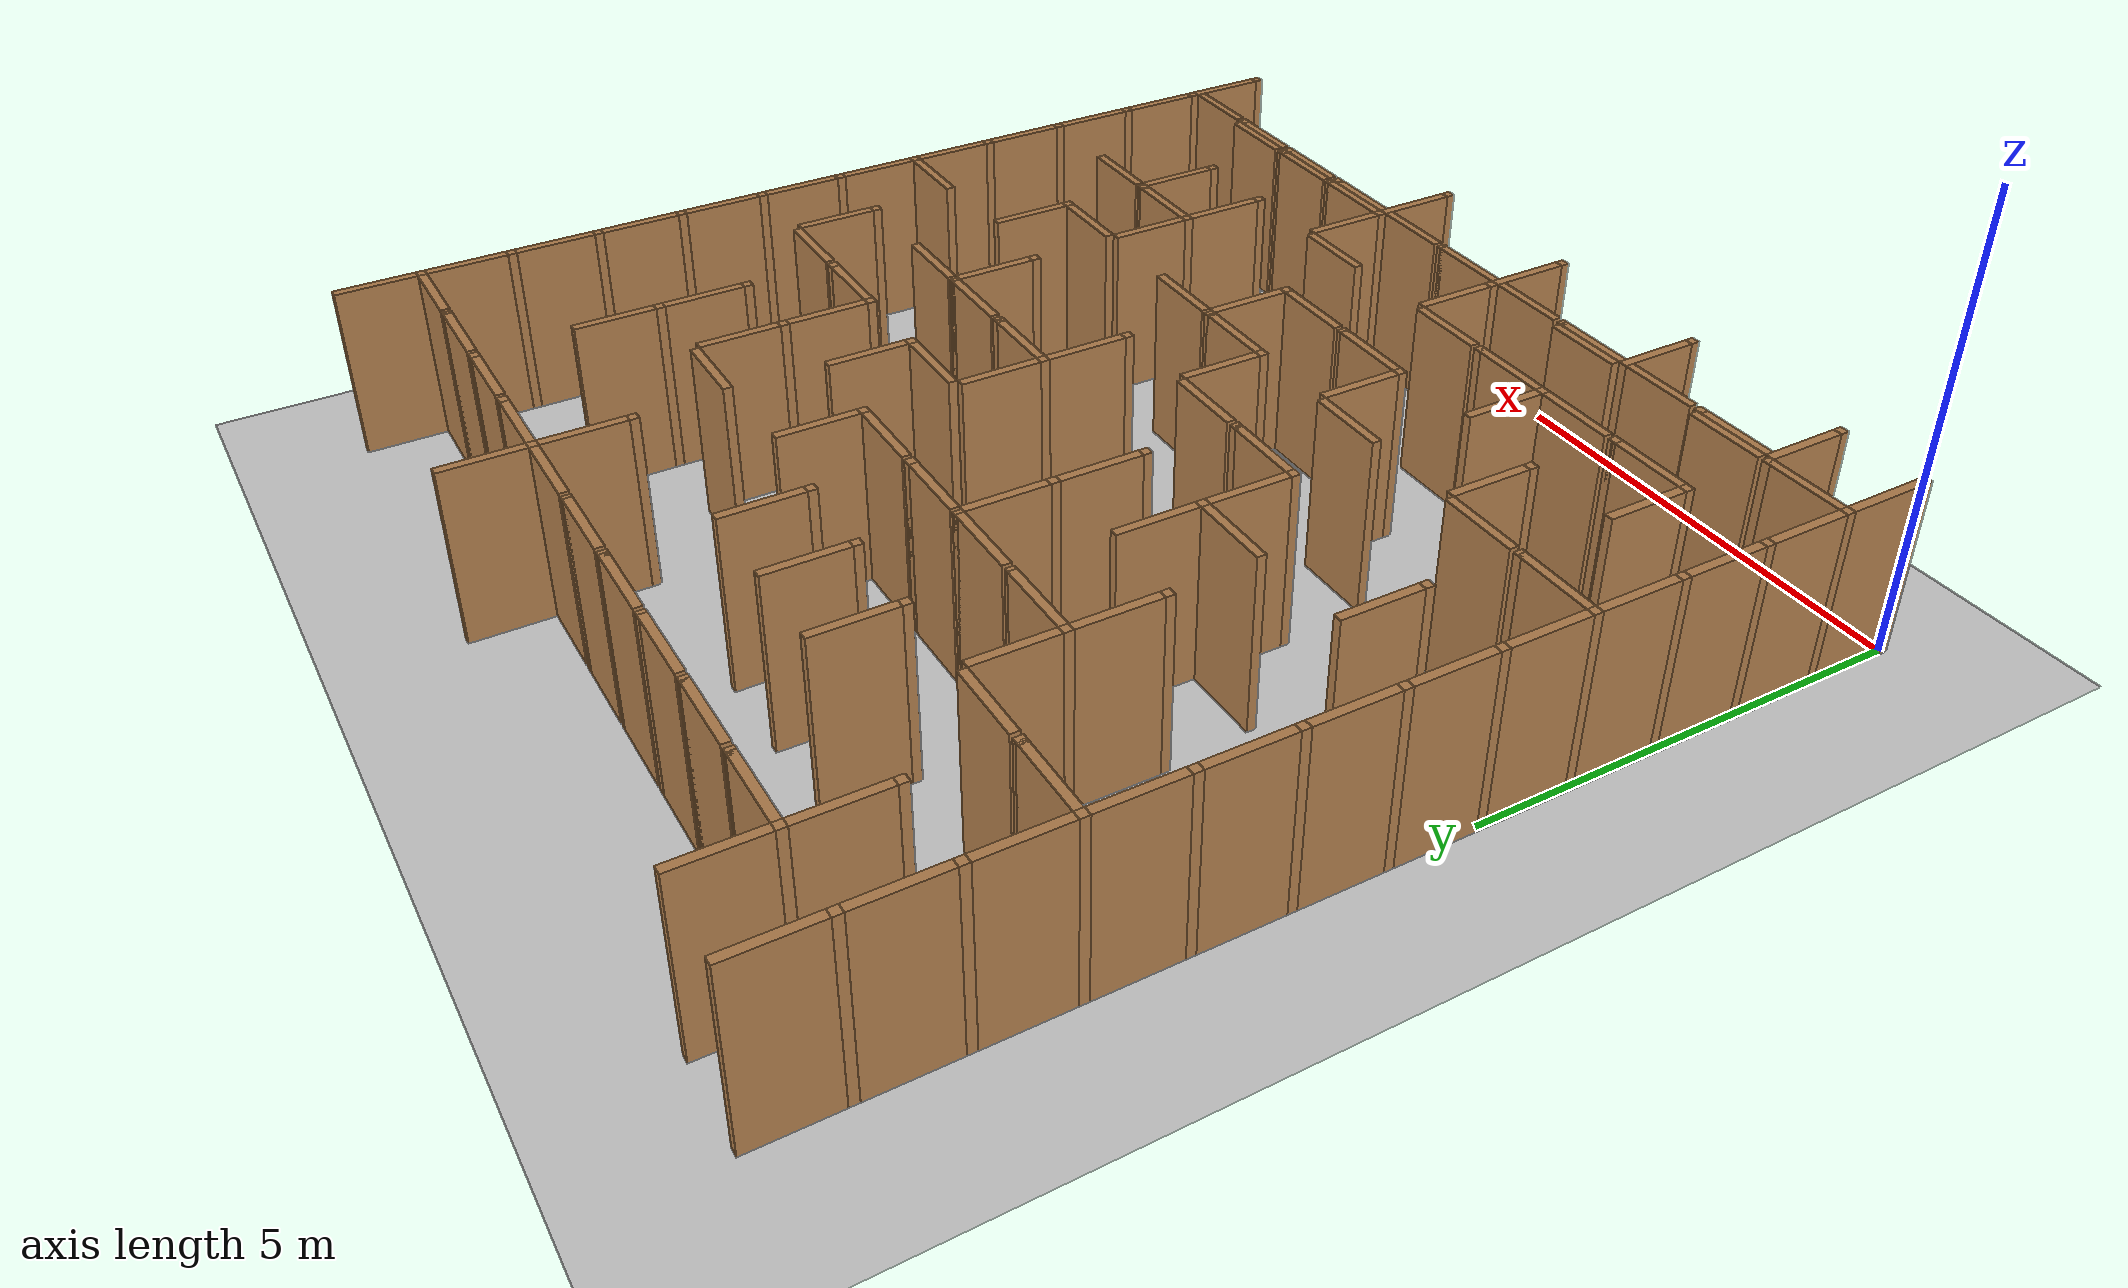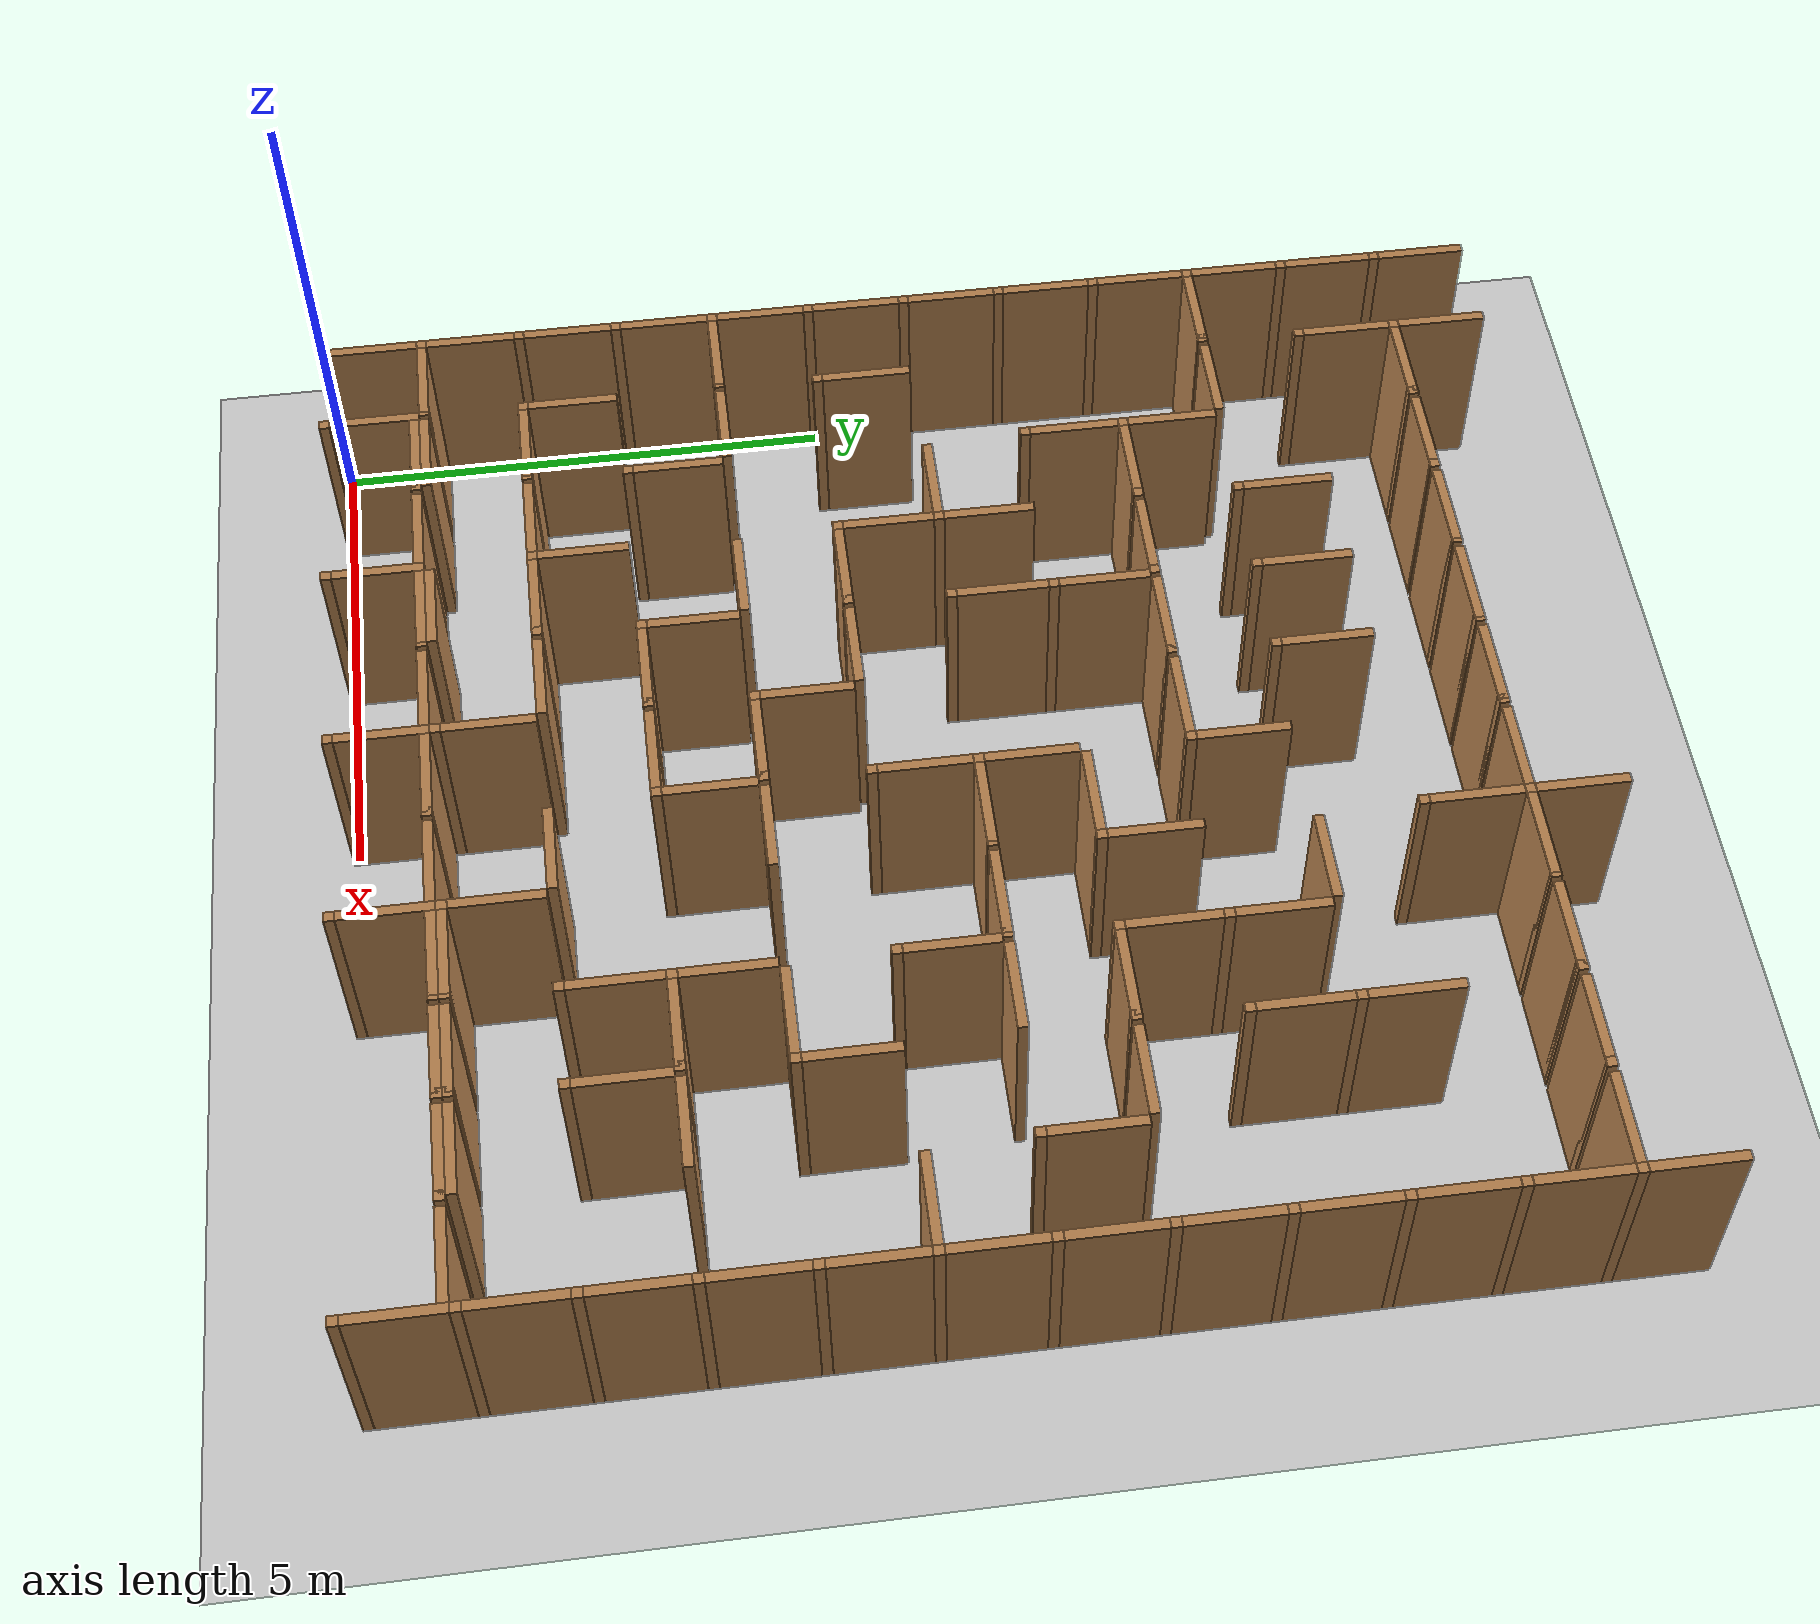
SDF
<?xml version='1.0' encoding='UTF-8'?>
<sdf version="1.6">
  <world name="default">
    <include>
      <uri>model://sun</uri>
    </include>
    <model name="ground_plane">
      <static>true</static>
      <link name="link">
        <collision name="collision">
          <geometry>
            <plane>
              <size>12.0 12.0</size>
            </plane>
          </geometry>
        </collision>
        <visual name="visual">
          <cast_shadows>false</cast_shadows>
          <geometry>
            <plane>
              <size>12.0 12.0</size>
            </plane>
          </geometry>
          <material>
            <script>
              <uri>file://media/materials/scripts/gazebo.material</uri>
              <name>Gazebo/Grey</name>
            </script>
          </material>
        </visual>
      </link>
      <pose>6.0 6.0 0 0 0 0</pose>
    </model>
    <model name="vwall_0_0">
      <pose>0.0 0.5 1.0 0 0 0</pose>
      <link name="link">
        <collision name="collision">
          <geometry>
            <box>
              <size>0.1 0.9 2</size>
            </box>
          </geometry>
        </collision>
        <visual name="visual">
          <geometry>
            <box>
              <size>0.1 0.9 2</size>
            </box>
          </geometry>
          <material>
            <script>
              <uri>file://media/materials/scripts/gazebo.material</uri>
              <name>Gazebo/Wood</name>
            </script>
          </material>
        </visual>
      </link>
    </model>
    <model name="joint_0.0_0.0">
      <pose>0.0 0.0 1.0 0 0 0</pose>
      <link name="link">
        <collision name="collision">
          <geometry>
            <box>
              <size>0.1 0.1 2</size>
            </box>
          </geometry>
        </collision>
        <visual name="visual">
          <geometry>
            <box>
              <size>0.1 0.1 2</size>
            </box>
          </geometry>
          <material>
            <script>
              <uri>file://media/materials/scripts/gazebo.material</uri>
              <name>Gazebo/Wood</name>
            </script>
          </material>
        </visual>
      </link>
    </model>
    <model name="vwall_0_1">
      <pose>1.0 0.5 1.0 0 0 0</pose>
      <link name="link">
        <collision name="collision">
          <geometry>
            <box>
              <size>0.1 0.9 2</size>
            </box>
          </geometry>
        </collision>
        <visual name="visual">
          <geometry>
            <box>
              <size>0.1 0.9 2</size>
            </box>
          </geometry>
          <material>
            <script>
              <uri>file://media/materials/scripts/gazebo.material</uri>
              <name>Gazebo/Wood</name>
            </script>
          </material>
        </visual>
      </link>
    </model>
    <model name="joint_1.0_0.0">
      <pose>1.0 0.0 1.0 0 0 0</pose>
      <link name="link">
        <collision name="collision">
          <geometry>
            <box>
              <size>0.1 0.1 2</size>
            </box>
          </geometry>
        </collision>
        <visual name="visual">
          <geometry>
            <box>
              <size>0.1 0.1 2</size>
            </box>
          </geometry>
          <material>
            <script>
              <uri>file://media/materials/scripts/gazebo.material</uri>
              <name>Gazebo/Wood</name>
            </script>
          </material>
        </visual>
      </link>
    </model>
    <model name="vwall_0_3">
      <pose>3.0 0.5 1.0 0 0 0</pose>
      <link name="link">
        <collision name="collision">
          <geometry>
            <box>
              <size>0.1 0.9 2</size>
            </box>
          </geometry>
        </collision>
        <visual name="visual">
          <geometry>
            <box>
              <size>0.1 0.9 2</size>
            </box>
          </geometry>
          <material>
            <script>
              <uri>file://media/materials/scripts/gazebo.material</uri>
              <name>Gazebo/Wood</name>
            </script>
          </material>
        </visual>
      </link>
    </model>
    <model name="joint_3.0_0.0">
      <pose>3.0 0.0 1.0 0 0 0</pose>
      <link name="link">
        <collision name="collision">
          <geometry>
            <box>
              <size>0.1 0.1 2</size>
            </box>
          </geometry>
        </collision>
        <visual name="visual">
          <geometry>
            <box>
              <size>0.1 0.1 2</size>
            </box>
          </geometry>
          <material>
            <script>
              <uri>file://media/materials/scripts/gazebo.material</uri>
              <name>Gazebo/Wood</name>
            </script>
          </material>
        </visual>
      </link>
    </model>
    <model name="vwall_0_5">
      <pose>5.0 0.5 1.0 0 0 0</pose>
      <link name="link">
        <collision name="collision">
          <geometry>
            <box>
              <size>0.1 0.9 2</size>
            </box>
          </geometry>
        </collision>
        <visual name="visual">
          <geometry>
            <box>
              <size>0.1 0.9 2</size>
            </box>
          </geometry>
          <material>
            <script>
              <uri>file://media/materials/scripts/gazebo.material</uri>
              <name>Gazebo/Wood</name>
            </script>
          </material>
        </visual>
      </link>
    </model>
    <model name="joint_5.0_0.0">
      <pose>5.0 0.0 1.0 0 0 0</pose>
      <link name="link">
        <collision name="collision">
          <geometry>
            <box>
              <size>0.1 0.1 2</size>
            </box>
          </geometry>
        </collision>
        <visual name="visual">
          <geometry>
            <box>
              <size>0.1 0.1 2</size>
            </box>
          </geometry>
          <material>
            <script>
              <uri>file://media/materials/scripts/gazebo.material</uri>
              <name>Gazebo/Wood</name>
            </script>
          </material>
        </visual>
      </link>
    </model>
    <model name="vwall_0_7">
      <pose>7.0 0.5 1.0 0 0 0</pose>
      <link name="link">
        <collision name="collision">
          <geometry>
            <box>
              <size>0.1 0.9 2</size>
            </box>
          </geometry>
        </collision>
        <visual name="visual">
          <geometry>
            <box>
              <size>0.1 0.9 2</size>
            </box>
          </geometry>
          <material>
            <script>
              <uri>file://media/materials/scripts/gazebo.material</uri>
              <name>Gazebo/Wood</name>
            </script>
          </material>
        </visual>
      </link>
    </model>
    <model name="joint_7.0_0.0">
      <pose>7.0 0.0 1.0 0 0 0</pose>
      <link name="link">
        <collision name="collision">
          <geometry>
            <box>
              <size>0.1 0.1 2</size>
            </box>
          </geometry>
        </collision>
        <visual name="visual">
          <geometry>
            <box>
              <size>0.1 0.1 2</size>
            </box>
          </geometry>
          <material>
            <script>
              <uri>file://media/materials/scripts/gazebo.material</uri>
              <name>Gazebo/Wood</name>
            </script>
          </material>
        </visual>
      </link>
    </model>
    <model name="vwall_0_11">
      <pose>11.0 0.5 1.0 0 0 0</pose>
      <link name="link">
        <collision name="collision">
          <geometry>
            <box>
              <size>0.1 0.9 2</size>
            </box>
          </geometry>
        </collision>
        <visual name="visual">
          <geometry>
            <box>
              <size>0.1 0.9 2</size>
            </box>
          </geometry>
          <material>
            <script>
              <uri>file://media/materials/scripts/gazebo.material</uri>
              <name>Gazebo/Wood</name>
            </script>
          </material>
        </visual>
      </link>
    </model>
    <model name="joint_11.0_0.0">
      <pose>11.0 0.0 1.0 0 0 0</pose>
      <link name="link">
        <collision name="collision">
          <geometry>
            <box>
              <size>0.1 0.1 2</size>
            </box>
          </geometry>
        </collision>
        <visual name="visual">
          <geometry>
            <box>
              <size>0.1 0.1 2</size>
            </box>
          </geometry>
          <material>
            <script>
              <uri>file://media/materials/scripts/gazebo.material</uri>
              <name>Gazebo/Wood</name>
            </script>
          </material>
        </visual>
      </link>
    </model>
    <model name="vwall_1_0">
      <pose>0.0 1.5 1.0 0 0 0</pose>
      <link name="link">
        <collision name="collision">
          <geometry>
            <box>
              <size>0.1 0.9 2</size>
            </box>
          </geometry>
        </collision>
        <visual name="visual">
          <geometry>
            <box>
              <size>0.1 0.9 2</size>
            </box>
          </geometry>
          <material>
            <script>
              <uri>file://media/materials/scripts/gazebo.material</uri>
              <name>Gazebo/Wood</name>
            </script>
          </material>
        </visual>
      </link>
    </model>
    <model name="joint_0.0_1.0">
      <pose>0.0 1.0 1.0 0 0 0</pose>
      <link name="link">
        <collision name="collision">
          <geometry>
            <box>
              <size>0.1 0.1 2</size>
            </box>
          </geometry>
        </collision>
        <visual name="visual">
          <geometry>
            <box>
              <size>0.1 0.1 2</size>
            </box>
          </geometry>
          <material>
            <script>
              <uri>file://media/materials/scripts/gazebo.material</uri>
              <name>Gazebo/Wood</name>
            </script>
          </material>
        </visual>
      </link>
    </model>
    <model name="vwall_1_5">
      <pose>5.0 1.5 1.0 0 0 0</pose>
      <link name="link">
        <collision name="collision">
          <geometry>
            <box>
              <size>0.1 0.9 2</size>
            </box>
          </geometry>
        </collision>
        <visual name="visual">
          <geometry>
            <box>
              <size>0.1 0.9 2</size>
            </box>
          </geometry>
          <material>
            <script>
              <uri>file://media/materials/scripts/gazebo.material</uri>
              <name>Gazebo/Wood</name>
            </script>
          </material>
        </visual>
      </link>
    </model>
    <model name="joint_5.0_1.0">
      <pose>5.0 1.0 1.0 0 0 0</pose>
      <link name="link">
        <collision name="collision">
          <geometry>
            <box>
              <size>0.1 0.1 2</size>
            </box>
          </geometry>
        </collision>
        <visual name="visual">
          <geometry>
            <box>
              <size>0.1 0.1 2</size>
            </box>
          </geometry>
          <material>
            <script>
              <uri>file://media/materials/scripts/gazebo.material</uri>
              <name>Gazebo/Wood</name>
            </script>
          </material>
        </visual>
      </link>
    </model>
    <model name="vwall_1_7">
      <pose>7.0 1.5 1.0 0 0 0</pose>
      <link name="link">
        <collision name="collision">
          <geometry>
            <box>
              <size>0.1 0.9 2</size>
            </box>
          </geometry>
        </collision>
        <visual name="visual">
          <geometry>
            <box>
              <size>0.1 0.9 2</size>
            </box>
          </geometry>
          <material>
            <script>
              <uri>file://media/materials/scripts/gazebo.material</uri>
              <name>Gazebo/Wood</name>
            </script>
          </material>
        </visual>
      </link>
    </model>
    <model name="joint_7.0_1.0">
      <pose>7.0 1.0 1.0 0 0 0</pose>
      <link name="link">
        <collision name="collision">
          <geometry>
            <box>
              <size>0.1 0.1 2</size>
            </box>
          </geometry>
        </collision>
        <visual name="visual">
          <geometry>
            <box>
              <size>0.1 0.1 2</size>
            </box>
          </geometry>
          <material>
            <script>
              <uri>file://media/materials/scripts/gazebo.material</uri>
              <name>Gazebo/Wood</name>
            </script>
          </material>
        </visual>
      </link>
    </model>
    <model name="vwall_1_11">
      <pose>11.0 1.5 1.0 0 0 0</pose>
      <link name="link">
        <collision name="collision">
          <geometry>
            <box>
              <size>0.1 0.9 2</size>
            </box>
          </geometry>
        </collision>
        <visual name="visual">
          <geometry>
            <box>
              <size>0.1 0.9 2</size>
            </box>
          </geometry>
          <material>
            <script>
              <uri>file://media/materials/scripts/gazebo.material</uri>
              <name>Gazebo/Wood</name>
            </script>
          </material>
        </visual>
      </link>
    </model>
    <model name="joint_11.0_1.0">
      <pose>11.0 1.0 1.0 0 0 0</pose>
      <link name="link">
        <collision name="collision">
          <geometry>
            <box>
              <size>0.1 0.1 2</size>
            </box>
          </geometry>
        </collision>
        <visual name="visual">
          <geometry>
            <box>
              <size>0.1 0.1 2</size>
            </box>
          </geometry>
          <material>
            <script>
              <uri>file://media/materials/scripts/gazebo.material</uri>
              <name>Gazebo/Wood</name>
            </script>
          </material>
        </visual>
      </link>
    </model>
    <model name="vwall_2_0">
      <pose>0.0 2.5 1.0 0 0 0</pose>
      <link name="link">
        <collision name="collision">
          <geometry>
            <box>
              <size>0.1 0.9 2</size>
            </box>
          </geometry>
        </collision>
        <visual name="visual">
          <geometry>
            <box>
              <size>0.1 0.9 2</size>
            </box>
          </geometry>
          <material>
            <script>
              <uri>file://media/materials/scripts/gazebo.material</uri>
              <name>Gazebo/Wood</name>
            </script>
          </material>
        </visual>
      </link>
    </model>
    <model name="joint_0.0_2.0">
      <pose>0.0 2.0 1.0 0 0 0</pose>
      <link name="link">
        <collision name="collision">
          <geometry>
            <box>
              <size>0.1 0.1 2</size>
            </box>
          </geometry>
        </collision>
        <visual name="visual">
          <geometry>
            <box>
              <size>0.1 0.1 2</size>
            </box>
          </geometry>
          <material>
            <script>
              <uri>file://media/materials/scripts/gazebo.material</uri>
              <name>Gazebo/Wood</name>
            </script>
          </material>
        </visual>
      </link>
    </model>
    <model name="vwall_2_1">
      <pose>1.0 2.5 1.0 0 0 0</pose>
      <link name="link">
        <collision name="collision">
          <geometry>
            <box>
              <size>0.1 0.9 2</size>
            </box>
          </geometry>
        </collision>
        <visual name="visual">
          <geometry>
            <box>
              <size>0.1 0.9 2</size>
            </box>
          </geometry>
          <material>
            <script>
              <uri>file://media/materials/scripts/gazebo.material</uri>
              <name>Gazebo/Wood</name>
            </script>
          </material>
        </visual>
      </link>
    </model>
    <model name="joint_1.0_2.0">
      <pose>1.0 2.0 1.0 0 0 0</pose>
      <link name="link">
        <collision name="collision">
          <geometry>
            <box>
              <size>0.1 0.1 2</size>
            </box>
          </geometry>
        </collision>
        <visual name="visual">
          <geometry>
            <box>
              <size>0.1 0.1 2</size>
            </box>
          </geometry>
          <material>
            <script>
              <uri>file://media/materials/scripts/gazebo.material</uri>
              <name>Gazebo/Wood</name>
            </script>
          </material>
        </visual>
      </link>
    </model>
    <model name="vwall_2_3">
      <pose>3.0 2.5 1.0 0 0 0</pose>
      <link name="link">
        <collision name="collision">
          <geometry>
            <box>
              <size>0.1 0.9 2</size>
            </box>
          </geometry>
        </collision>
        <visual name="visual">
          <geometry>
            <box>
              <size>0.1 0.9 2</size>
            </box>
          </geometry>
          <material>
            <script>
              <uri>file://media/materials/scripts/gazebo.material</uri>
              <name>Gazebo/Wood</name>
            </script>
          </material>
        </visual>
      </link>
    </model>
    <model name="joint_3.0_2.0">
      <pose>3.0 2.0 1.0 0 0 0</pose>
      <link name="link">
        <collision name="collision">
          <geometry>
            <box>
              <size>0.1 0.1 2</size>
            </box>
          </geometry>
        </collision>
        <visual name="visual">
          <geometry>
            <box>
              <size>0.1 0.1 2</size>
            </box>
          </geometry>
          <material>
            <script>
              <uri>file://media/materials/scripts/gazebo.material</uri>
              <name>Gazebo/Wood</name>
            </script>
          </material>
        </visual>
      </link>
    </model>
    <model name="vwall_2_8">
      <pose>8.0 2.5 1.0 0 0 0</pose>
      <link name="link">
        <collision name="collision">
          <geometry>
            <box>
              <size>0.1 0.9 2</size>
            </box>
          </geometry>
        </collision>
        <visual name="visual">
          <geometry>
            <box>
              <size>0.1 0.9 2</size>
            </box>
          </geometry>
          <material>
            <script>
              <uri>file://media/materials/scripts/gazebo.material</uri>
              <name>Gazebo/Wood</name>
            </script>
          </material>
        </visual>
      </link>
    </model>
    <model name="joint_8.0_2.0">
      <pose>8.0 2.0 1.0 0 0 0</pose>
      <link name="link">
        <collision name="collision">
          <geometry>
            <box>
              <size>0.1 0.1 2</size>
            </box>
          </geometry>
        </collision>
        <visual name="visual">
          <geometry>
            <box>
              <size>0.1 0.1 2</size>
            </box>
          </geometry>
          <material>
            <script>
              <uri>file://media/materials/scripts/gazebo.material</uri>
              <name>Gazebo/Wood</name>
            </script>
          </material>
        </visual>
      </link>
    </model>
    <model name="vwall_2_9">
      <pose>9.0 2.5 1.0 0 0 0</pose>
      <link name="link">
        <collision name="collision">
          <geometry>
            <box>
              <size>0.1 0.9 2</size>
            </box>
          </geometry>
        </collision>
        <visual name="visual">
          <geometry>
            <box>
              <size>0.1 0.9 2</size>
            </box>
          </geometry>
          <material>
            <script>
              <uri>file://media/materials/scripts/gazebo.material</uri>
              <name>Gazebo/Wood</name>
            </script>
          </material>
        </visual>
      </link>
    </model>
    <model name="joint_9.0_2.0">
      <pose>9.0 2.0 1.0 0 0 0</pose>
      <link name="link">
        <collision name="collision">
          <geometry>
            <box>
              <size>0.1 0.1 2</size>
            </box>
          </geometry>
        </collision>
        <visual name="visual">
          <geometry>
            <box>
              <size>0.1 0.1 2</size>
            </box>
          </geometry>
          <material>
            <script>
              <uri>file://media/materials/scripts/gazebo.material</uri>
              <name>Gazebo/Wood</name>
            </script>
          </material>
        </visual>
      </link>
    </model>
    <model name="vwall_2_11">
      <pose>11.0 2.5 1.0 0 0 0</pose>
      <link name="link">
        <collision name="collision">
          <geometry>
            <box>
              <size>0.1 0.9 2</size>
            </box>
          </geometry>
        </collision>
        <visual name="visual">
          <geometry>
            <box>
              <size>0.1 0.9 2</size>
            </box>
          </geometry>
          <material>
            <script>
              <uri>file://media/materials/scripts/gazebo.material</uri>
              <name>Gazebo/Wood</name>
            </script>
          </material>
        </visual>
      </link>
    </model>
    <model name="joint_11.0_2.0">
      <pose>11.0 2.0 1.0 0 0 0</pose>
      <link name="link">
        <collision name="collision">
          <geometry>
            <box>
              <size>0.1 0.1 2</size>
            </box>
          </geometry>
        </collision>
        <visual name="visual">
          <geometry>
            <box>
              <size>0.1 0.1 2</size>
            </box>
          </geometry>
          <material>
            <script>
              <uri>file://media/materials/scripts/gazebo.material</uri>
              <name>Gazebo/Wood</name>
            </script>
          </material>
        </visual>
      </link>
    </model>
    <model name="vwall_3_0">
      <pose>0.0 3.5 1.0 0 0 0</pose>
      <link name="link">
        <collision name="collision">
          <geometry>
            <box>
              <size>0.1 0.9 2</size>
            </box>
          </geometry>
        </collision>
        <visual name="visual">
          <geometry>
            <box>
              <size>0.1 0.9 2</size>
            </box>
          </geometry>
          <material>
            <script>
              <uri>file://media/materials/scripts/gazebo.material</uri>
              <name>Gazebo/Wood</name>
            </script>
          </material>
        </visual>
      </link>
    </model>
    <model name="joint_0.0_3.0">
      <pose>0.0 3.0 1.0 0 0 0</pose>
      <link name="link">
        <collision name="collision">
          <geometry>
            <box>
              <size>0.1 0.1 2</size>
            </box>
          </geometry>
        </collision>
        <visual name="visual">
          <geometry>
            <box>
              <size>0.1 0.1 2</size>
            </box>
          </geometry>
          <material>
            <script>
              <uri>file://media/materials/scripts/gazebo.material</uri>
              <name>Gazebo/Wood</name>
            </script>
          </material>
        </visual>
      </link>
    </model>
    <model name="vwall_3_2">
      <pose>2.0 3.5 1.0 0 0 0</pose>
      <link name="link">
        <collision name="collision">
          <geometry>
            <box>
              <size>0.1 0.9 2</size>
            </box>
          </geometry>
        </collision>
        <visual name="visual">
          <geometry>
            <box>
              <size>0.1 0.9 2</size>
            </box>
          </geometry>
          <material>
            <script>
              <uri>file://media/materials/scripts/gazebo.material</uri>
              <name>Gazebo/Wood</name>
            </script>
          </material>
        </visual>
      </link>
    </model>
    <model name="joint_2.0_3.0">
      <pose>2.0 3.0 1.0 0 0 0</pose>
      <link name="link">
        <collision name="collision">
          <geometry>
            <box>
              <size>0.1 0.1 2</size>
            </box>
          </geometry>
        </collision>
        <visual name="visual">
          <geometry>
            <box>
              <size>0.1 0.1 2</size>
            </box>
          </geometry>
          <material>
            <script>
              <uri>file://media/materials/scripts/gazebo.material</uri>
              <name>Gazebo/Wood</name>
            </script>
          </material>
        </visual>
      </link>
    </model>
    <model name="vwall_3_4">
      <pose>4.0 3.5 1.0 0 0 0</pose>
      <link name="link">
        <collision name="collision">
          <geometry>
            <box>
              <size>0.1 0.9 2</size>
            </box>
          </geometry>
        </collision>
        <visual name="visual">
          <geometry>
            <box>
              <size>0.1 0.9 2</size>
            </box>
          </geometry>
          <material>
            <script>
              <uri>file://media/materials/scripts/gazebo.material</uri>
              <name>Gazebo/Wood</name>
            </script>
          </material>
        </visual>
      </link>
    </model>
    <model name="joint_4.0_3.0">
      <pose>4.0 3.0 1.0 0 0 0</pose>
      <link name="link">
        <collision name="collision">
          <geometry>
            <box>
              <size>0.1 0.1 2</size>
            </box>
          </geometry>
        </collision>
        <visual name="visual">
          <geometry>
            <box>
              <size>0.1 0.1 2</size>
            </box>
          </geometry>
          <material>
            <script>
              <uri>file://media/materials/scripts/gazebo.material</uri>
              <name>Gazebo/Wood</name>
            </script>
          </material>
        </visual>
      </link>
    </model>
    <model name="vwall_3_6">
      <pose>6.0 3.5 1.0 0 0 0</pose>
      <link name="link">
        <collision name="collision">
          <geometry>
            <box>
              <size>0.1 0.9 2</size>
            </box>
          </geometry>
        </collision>
        <visual name="visual">
          <geometry>
            <box>
              <size>0.1 0.9 2</size>
            </box>
          </geometry>
          <material>
            <script>
              <uri>file://media/materials/scripts/gazebo.material</uri>
              <name>Gazebo/Wood</name>
            </script>
          </material>
        </visual>
      </link>
    </model>
    <model name="joint_6.0_3.0">
      <pose>6.0 3.0 1.0 0 0 0</pose>
      <link name="link">
        <collision name="collision">
          <geometry>
            <box>
              <size>0.1 0.1 2</size>
            </box>
          </geometry>
        </collision>
        <visual name="visual">
          <geometry>
            <box>
              <size>0.1 0.1 2</size>
            </box>
          </geometry>
          <material>
            <script>
              <uri>file://media/materials/scripts/gazebo.material</uri>
              <name>Gazebo/Wood</name>
            </script>
          </material>
        </visual>
      </link>
    </model>
    <model name="vwall_3_8">
      <pose>8.0 3.5 1.0 0 0 0</pose>
      <link name="link">
        <collision name="collision">
          <geometry>
            <box>
              <size>0.1 0.9 2</size>
            </box>
          </geometry>
        </collision>
        <visual name="visual">
          <geometry>
            <box>
              <size>0.1 0.9 2</size>
            </box>
          </geometry>
          <material>
            <script>
              <uri>file://media/materials/scripts/gazebo.material</uri>
              <name>Gazebo/Wood</name>
            </script>
          </material>
        </visual>
      </link>
    </model>
    <model name="joint_8.0_3.0">
      <pose>8.0 3.0 1.0 0 0 0</pose>
      <link name="link">
        <collision name="collision">
          <geometry>
            <box>
              <size>0.1 0.1 2</size>
            </box>
          </geometry>
        </collision>
        <visual name="visual">
          <geometry>
            <box>
              <size>0.1 0.1 2</size>
            </box>
          </geometry>
          <material>
            <script>
              <uri>file://media/materials/scripts/gazebo.material</uri>
              <name>Gazebo/Wood</name>
            </script>
          </material>
        </visual>
      </link>
    </model>
    <model name="vwall_3_11">
      <pose>11.0 3.5 1.0 0 0 0</pose>
      <link name="link">
        <collision name="collision">
          <geometry>
            <box>
              <size>0.1 0.9 2</size>
            </box>
          </geometry>
        </collision>
        <visual name="visual">
          <geometry>
            <box>
              <size>0.1 0.9 2</size>
            </box>
          </geometry>
          <material>
            <script>
              <uri>file://media/materials/scripts/gazebo.material</uri>
              <name>Gazebo/Wood</name>
            </script>
          </material>
        </visual>
      </link>
    </model>
    <model name="joint_11.0_3.0">
      <pose>11.0 3.0 1.0 0 0 0</pose>
      <link name="link">
        <collision name="collision">
          <geometry>
            <box>
              <size>0.1 0.1 2</size>
            </box>
          </geometry>
        </collision>
        <visual name="visual">
          <geometry>
            <box>
              <size>0.1 0.1 2</size>
            </box>
          </geometry>
          <material>
            <script>
              <uri>file://media/materials/scripts/gazebo.material</uri>
              <name>Gazebo/Wood</name>
            </script>
          </material>
        </visual>
      </link>
    </model>
    <model name="vwall_4_0">
      <pose>0.0 4.5 1.0 0 0 0</pose>
      <link name="link">
        <collision name="collision">
          <geometry>
            <box>
              <size>0.1 0.9 2</size>
            </box>
          </geometry>
        </collision>
        <visual name="visual">
          <geometry>
            <box>
              <size>0.1 0.9 2</size>
            </box>
          </geometry>
          <material>
            <script>
              <uri>file://media/materials/scripts/gazebo.material</uri>
              <name>Gazebo/Wood</name>
            </script>
          </material>
        </visual>
      </link>
    </model>
    <model name="joint_0.0_4.0">
      <pose>0.0 4.0 1.0 0 0 0</pose>
      <link name="link">
        <collision name="collision">
          <geometry>
            <box>
              <size>0.1 0.1 2</size>
            </box>
          </geometry>
        </collision>
        <visual name="visual">
          <geometry>
            <box>
              <size>0.1 0.1 2</size>
            </box>
          </geometry>
          <material>
            <script>
              <uri>file://media/materials/scripts/gazebo.material</uri>
              <name>Gazebo/Wood</name>
            </script>
          </material>
        </visual>
      </link>
    </model>
    <model name="vwall_4_5">
      <pose>5.0 4.5 1.0 0 0 0</pose>
      <link name="link">
        <collision name="collision">
          <geometry>
            <box>
              <size>0.1 0.9 2</size>
            </box>
          </geometry>
        </collision>
        <visual name="visual">
          <geometry>
            <box>
              <size>0.1 0.9 2</size>
            </box>
          </geometry>
          <material>
            <script>
              <uri>file://media/materials/scripts/gazebo.material</uri>
              <name>Gazebo/Wood</name>
            </script>
          </material>
        </visual>
      </link>
    </model>
    <model name="joint_5.0_4.0">
      <pose>5.0 4.0 1.0 0 0 0</pose>
      <link name="link">
        <collision name="collision">
          <geometry>
            <box>
              <size>0.1 0.1 2</size>
            </box>
          </geometry>
        </collision>
        <visual name="visual">
          <geometry>
            <box>
              <size>0.1 0.1 2</size>
            </box>
          </geometry>
          <material>
            <script>
              <uri>file://media/materials/scripts/gazebo.material</uri>
              <name>Gazebo/Wood</name>
            </script>
          </material>
        </visual>
      </link>
    </model>
    <model name="vwall_4_9">
      <pose>9.0 4.5 1.0 0 0 0</pose>
      <link name="link">
        <collision name="collision">
          <geometry>
            <box>
              <size>0.1 0.9 2</size>
            </box>
          </geometry>
        </collision>
        <visual name="visual">
          <geometry>
            <box>
              <size>0.1 0.9 2</size>
            </box>
          </geometry>
          <material>
            <script>
              <uri>file://media/materials/scripts/gazebo.material</uri>
              <name>Gazebo/Wood</name>
            </script>
          </material>
        </visual>
      </link>
    </model>
    <model name="joint_9.0_4.0">
      <pose>9.0 4.0 1.0 0 0 0</pose>
      <link name="link">
        <collision name="collision">
          <geometry>
            <box>
              <size>0.1 0.1 2</size>
            </box>
          </geometry>
        </collision>
        <visual name="visual">
          <geometry>
            <box>
              <size>0.1 0.1 2</size>
            </box>
          </geometry>
          <material>
            <script>
              <uri>file://media/materials/scripts/gazebo.material</uri>
              <name>Gazebo/Wood</name>
            </script>
          </material>
        </visual>
      </link>
    </model>
    <model name="vwall_4_11">
      <pose>11.0 4.5 1.0 0 0 0</pose>
      <link name="link">
        <collision name="collision">
          <geometry>
            <box>
              <size>0.1 0.9 2</size>
            </box>
          </geometry>
        </collision>
        <visual name="visual">
          <geometry>
            <box>
              <size>0.1 0.9 2</size>
            </box>
          </geometry>
          <material>
            <script>
              <uri>file://media/materials/scripts/gazebo.material</uri>
              <name>Gazebo/Wood</name>
            </script>
          </material>
        </visual>
      </link>
    </model>
    <model name="joint_11.0_4.0">
      <pose>11.0 4.0 1.0 0 0 0</pose>
      <link name="link">
        <collision name="collision">
          <geometry>
            <box>
              <size>0.1 0.1 2</size>
            </box>
          </geometry>
        </collision>
        <visual name="visual">
          <geometry>
            <box>
              <size>0.1 0.1 2</size>
            </box>
          </geometry>
          <material>
            <script>
              <uri>file://media/materials/scripts/gazebo.material</uri>
              <name>Gazebo/Wood</name>
            </script>
          </material>
        </visual>
      </link>
    </model>
    <model name="vwall_5_0">
      <pose>0.0 5.5 1.0 0 0 0</pose>
      <link name="link">
        <collision name="collision">
          <geometry>
            <box>
              <size>0.1 0.9 2</size>
            </box>
          </geometry>
        </collision>
        <visual name="visual">
          <geometry>
            <box>
              <size>0.1 0.9 2</size>
            </box>
          </geometry>
          <material>
            <script>
              <uri>file://media/materials/scripts/gazebo.material</uri>
              <name>Gazebo/Wood</name>
            </script>
          </material>
        </visual>
      </link>
    </model>
    <model name="joint_0.0_5.0">
      <pose>0.0 5.0 1.0 0 0 0</pose>
      <link name="link">
        <collision name="collision">
          <geometry>
            <box>
              <size>0.1 0.1 2</size>
            </box>
          </geometry>
        </collision>
        <visual name="visual">
          <geometry>
            <box>
              <size>0.1 0.1 2</size>
            </box>
          </geometry>
          <material>
            <script>
              <uri>file://media/materials/scripts/gazebo.material</uri>
              <name>Gazebo/Wood</name>
            </script>
          </material>
        </visual>
      </link>
    </model>
    <model name="vwall_5_1">
      <pose>1.0 5.5 1.0 0 0 0</pose>
      <link name="link">
        <collision name="collision">
          <geometry>
            <box>
              <size>0.1 0.9 2</size>
            </box>
          </geometry>
        </collision>
        <visual name="visual">
          <geometry>
            <box>
              <size>0.1 0.9 2</size>
            </box>
          </geometry>
          <material>
            <script>
              <uri>file://media/materials/scripts/gazebo.material</uri>
              <name>Gazebo/Wood</name>
            </script>
          </material>
        </visual>
      </link>
    </model>
    <model name="joint_1.0_5.0">
      <pose>1.0 5.0 1.0 0 0 0</pose>
      <link name="link">
        <collision name="collision">
          <geometry>
            <box>
              <size>0.1 0.1 2</size>
            </box>
          </geometry>
        </collision>
        <visual name="visual">
          <geometry>
            <box>
              <size>0.1 0.1 2</size>
            </box>
          </geometry>
          <material>
            <script>
              <uri>file://media/materials/scripts/gazebo.material</uri>
              <name>Gazebo/Wood</name>
            </script>
          </material>
        </visual>
      </link>
    </model>
    <model name="vwall_5_3">
      <pose>3.0 5.5 1.0 0 0 0</pose>
      <link name="link">
        <collision name="collision">
          <geometry>
            <box>
              <size>0.1 0.9 2</size>
            </box>
          </geometry>
        </collision>
        <visual name="visual">
          <geometry>
            <box>
              <size>0.1 0.9 2</size>
            </box>
          </geometry>
          <material>
            <script>
              <uri>file://media/materials/scripts/gazebo.material</uri>
              <name>Gazebo/Wood</name>
            </script>
          </material>
        </visual>
      </link>
    </model>
    <model name="joint_3.0_5.0">
      <pose>3.0 5.0 1.0 0 0 0</pose>
      <link name="link">
        <collision name="collision">
          <geometry>
            <box>
              <size>0.1 0.1 2</size>
            </box>
          </geometry>
        </collision>
        <visual name="visual">
          <geometry>
            <box>
              <size>0.1 0.1 2</size>
            </box>
          </geometry>
          <material>
            <script>
              <uri>file://media/materials/scripts/gazebo.material</uri>
              <name>Gazebo/Wood</name>
            </script>
          </material>
        </visual>
      </link>
    </model>
    <model name="vwall_5_6">
      <pose>6.0 5.5 1.0 0 0 0</pose>
      <link name="link">
        <collision name="collision">
          <geometry>
            <box>
              <size>0.1 0.9 2</size>
            </box>
          </geometry>
        </collision>
        <visual name="visual">
          <geometry>
            <box>
              <size>0.1 0.9 2</size>
            </box>
          </geometry>
          <material>
            <script>
              <uri>file://media/materials/scripts/gazebo.material</uri>
              <name>Gazebo/Wood</name>
            </script>
          </material>
        </visual>
      </link>
    </model>
    <model name="joint_6.0_5.0">
      <pose>6.0 5.0 1.0 0 0 0</pose>
      <link name="link">
        <collision name="collision">
          <geometry>
            <box>
              <size>0.1 0.1 2</size>
            </box>
          </geometry>
        </collision>
        <visual name="visual">
          <geometry>
            <box>
              <size>0.1 0.1 2</size>
            </box>
          </geometry>
          <material>
            <script>
              <uri>file://media/materials/scripts/gazebo.material</uri>
              <name>Gazebo/Wood</name>
            </script>
          </material>
        </visual>
      </link>
    </model>
    <model name="vwall_5_8">
      <pose>8.0 5.5 1.0 0 0 0</pose>
      <link name="link">
        <collision name="collision">
          <geometry>
            <box>
              <size>0.1 0.9 2</size>
            </box>
          </geometry>
        </collision>
        <visual name="visual">
          <geometry>
            <box>
              <size>0.1 0.9 2</size>
            </box>
          </geometry>
          <material>
            <script>
              <uri>file://media/materials/scripts/gazebo.material</uri>
              <name>Gazebo/Wood</name>
            </script>
          </material>
        </visual>
      </link>
    </model>
    <model name="joint_8.0_5.0">
      <pose>8.0 5.0 1.0 0 0 0</pose>
      <link name="link">
        <collision name="collision">
          <geometry>
            <box>
              <size>0.1 0.1 2</size>
            </box>
          </geometry>
        </collision>
        <visual name="visual">
          <geometry>
            <box>
              <size>0.1 0.1 2</size>
            </box>
          </geometry>
          <material>
            <script>
              <uri>file://media/materials/scripts/gazebo.material</uri>
              <name>Gazebo/Wood</name>
            </script>
          </material>
        </visual>
      </link>
    </model>
    <model name="vwall_5_11">
      <pose>11.0 5.5 1.0 0 0 0</pose>
      <link name="link">
        <collision name="collision">
          <geometry>
            <box>
              <size>0.1 0.9 2</size>
            </box>
          </geometry>
        </collision>
        <visual name="visual">
          <geometry>
            <box>
              <size>0.1 0.9 2</size>
            </box>
          </geometry>
          <material>
            <script>
              <uri>file://media/materials/scripts/gazebo.material</uri>
              <name>Gazebo/Wood</name>
            </script>
          </material>
        </visual>
      </link>
    </model>
    <model name="joint_11.0_5.0">
      <pose>11.0 5.0 1.0 0 0 0</pose>
      <link name="link">
        <collision name="collision">
          <geometry>
            <box>
              <size>0.1 0.1 2</size>
            </box>
          </geometry>
        </collision>
        <visual name="visual">
          <geometry>
            <box>
              <size>0.1 0.1 2</size>
            </box>
          </geometry>
          <material>
            <script>
              <uri>file://media/materials/scripts/gazebo.material</uri>
              <name>Gazebo/Wood</name>
            </script>
          </material>
        </visual>
      </link>
    </model>
    <model name="vwall_6_0">
      <pose>0.0 6.5 1.0 0 0 0</pose>
      <link name="link">
        <collision name="collision">
          <geometry>
            <box>
              <size>0.1 0.9 2</size>
            </box>
          </geometry>
        </collision>
        <visual name="visual">
          <geometry>
            <box>
              <size>0.1 0.9 2</size>
            </box>
          </geometry>
          <material>
            <script>
              <uri>file://media/materials/scripts/gazebo.material</uri>
              <name>Gazebo/Wood</name>
            </script>
          </material>
        </visual>
      </link>
    </model>
    <model name="joint_0.0_6.0">
      <pose>0.0 6.0 1.0 0 0 0</pose>
      <link name="link">
        <collision name="collision">
          <geometry>
            <box>
              <size>0.1 0.1 2</size>
            </box>
          </geometry>
        </collision>
        <visual name="visual">
          <geometry>
            <box>
              <size>0.1 0.1 2</size>
            </box>
          </geometry>
          <material>
            <script>
              <uri>file://media/materials/scripts/gazebo.material</uri>
              <name>Gazebo/Wood</name>
            </script>
          </material>
        </visual>
      </link>
    </model>
    <model name="vwall_6_3">
      <pose>3.0 6.5 1.0 0 0 0</pose>
      <link name="link">
        <collision name="collision">
          <geometry>
            <box>
              <size>0.1 0.9 2</size>
            </box>
          </geometry>
        </collision>
        <visual name="visual">
          <geometry>
            <box>
              <size>0.1 0.9 2</size>
            </box>
          </geometry>
          <material>
            <script>
              <uri>file://media/materials/scripts/gazebo.material</uri>
              <name>Gazebo/Wood</name>
            </script>
          </material>
        </visual>
      </link>
    </model>
    <model name="joint_3.0_6.0">
      <pose>3.0 6.0 1.0 0 0 0</pose>
      <link name="link">
        <collision name="collision">
          <geometry>
            <box>
              <size>0.1 0.1 2</size>
            </box>
          </geometry>
        </collision>
        <visual name="visual">
          <geometry>
            <box>
              <size>0.1 0.1 2</size>
            </box>
          </geometry>
          <material>
            <script>
              <uri>file://media/materials/scripts/gazebo.material</uri>
              <name>Gazebo/Wood</name>
            </script>
          </material>
        </visual>
      </link>
    </model>
    <model name="vwall_6_4">
      <pose>4.0 6.5 1.0 0 0 0</pose>
      <link name="link">
        <collision name="collision">
          <geometry>
            <box>
              <size>0.1 0.9 2</size>
            </box>
          </geometry>
        </collision>
        <visual name="visual">
          <geometry>
            <box>
              <size>0.1 0.9 2</size>
            </box>
          </geometry>
          <material>
            <script>
              <uri>file://media/materials/scripts/gazebo.material</uri>
              <name>Gazebo/Wood</name>
            </script>
          </material>
        </visual>
      </link>
    </model>
    <model name="joint_4.0_6.0">
      <pose>4.0 6.0 1.0 0 0 0</pose>
      <link name="link">
        <collision name="collision">
          <geometry>
            <box>
              <size>0.1 0.1 2</size>
            </box>
          </geometry>
        </collision>
        <visual name="visual">
          <geometry>
            <box>
              <size>0.1 0.1 2</size>
            </box>
          </geometry>
          <material>
            <script>
              <uri>file://media/materials/scripts/gazebo.material</uri>
              <name>Gazebo/Wood</name>
            </script>
          </material>
        </visual>
      </link>
    </model>
    <model name="vwall_6_6">
      <pose>6.0 6.5 1.0 0 0 0</pose>
      <link name="link">
        <collision name="collision">
          <geometry>
            <box>
              <size>0.1 0.9 2</size>
            </box>
          </geometry>
        </collision>
        <visual name="visual">
          <geometry>
            <box>
              <size>0.1 0.9 2</size>
            </box>
          </geometry>
          <material>
            <script>
              <uri>file://media/materials/scripts/gazebo.material</uri>
              <name>Gazebo/Wood</name>
            </script>
          </material>
        </visual>
      </link>
    </model>
    <model name="joint_6.0_6.0">
      <pose>6.0 6.0 1.0 0 0 0</pose>
      <link name="link">
        <collision name="collision">
          <geometry>
            <box>
              <size>0.1 0.1 2</size>
            </box>
          </geometry>
        </collision>
        <visual name="visual">
          <geometry>
            <box>
              <size>0.1 0.1 2</size>
            </box>
          </geometry>
          <material>
            <script>
              <uri>file://media/materials/scripts/gazebo.material</uri>
              <name>Gazebo/Wood</name>
            </script>
          </material>
        </visual>
      </link>
    </model>
    <model name="vwall_6_10">
      <pose>10.0 6.5 1.0 0 0 0</pose>
      <link name="link">
        <collision name="collision">
          <geometry>
            <box>
              <size>0.1 0.9 2</size>
            </box>
          </geometry>
        </collision>
        <visual name="visual">
          <geometry>
            <box>
              <size>0.1 0.9 2</size>
            </box>
          </geometry>
          <material>
            <script>
              <uri>file://media/materials/scripts/gazebo.material</uri>
              <name>Gazebo/Wood</name>
            </script>
          </material>
        </visual>
      </link>
    </model>
    <model name="joint_10.0_6.0">
      <pose>10.0 6.0 1.0 0 0 0</pose>
      <link name="link">
        <collision name="collision">
          <geometry>
            <box>
              <size>0.1 0.1 2</size>
            </box>
          </geometry>
        </collision>
        <visual name="visual">
          <geometry>
            <box>
              <size>0.1 0.1 2</size>
            </box>
          </geometry>
          <material>
            <script>
              <uri>file://media/materials/scripts/gazebo.material</uri>
              <name>Gazebo/Wood</name>
            </script>
          </material>
        </visual>
      </link>
    </model>
    <model name="vwall_6_11">
      <pose>11.0 6.5 1.0 0 0 0</pose>
      <link name="link">
        <collision name="collision">
          <geometry>
            <box>
              <size>0.1 0.9 2</size>
            </box>
          </geometry>
        </collision>
        <visual name="visual">
          <geometry>
            <box>
              <size>0.1 0.9 2</size>
            </box>
          </geometry>
          <material>
            <script>
              <uri>file://media/materials/scripts/gazebo.material</uri>
              <name>Gazebo/Wood</name>
            </script>
          </material>
        </visual>
      </link>
    </model>
    <model name="joint_11.0_6.0">
      <pose>11.0 6.0 1.0 0 0 0</pose>
      <link name="link">
        <collision name="collision">
          <geometry>
            <box>
              <size>0.1 0.1 2</size>
            </box>
          </geometry>
        </collision>
        <visual name="visual">
          <geometry>
            <box>
              <size>0.1 0.1 2</size>
            </box>
          </geometry>
          <material>
            <script>
              <uri>file://media/materials/scripts/gazebo.material</uri>
              <name>Gazebo/Wood</name>
            </script>
          </material>
        </visual>
      </link>
    </model>
    <model name="vwall_7_0">
      <pose>0.0 7.5 1.0 0 0 0</pose>
      <link name="link">
        <collision name="collision">
          <geometry>
            <box>
              <size>0.1 0.9 2</size>
            </box>
          </geometry>
        </collision>
        <visual name="visual">
          <geometry>
            <box>
              <size>0.1 0.9 2</size>
            </box>
          </geometry>
          <material>
            <script>
              <uri>file://media/materials/scripts/gazebo.material</uri>
              <name>Gazebo/Wood</name>
            </script>
          </material>
        </visual>
      </link>
    </model>
    <model name="joint_0.0_7.0">
      <pose>0.0 7.0 1.0 0 0 0</pose>
      <link name="link">
        <collision name="collision">
          <geometry>
            <box>
              <size>0.1 0.1 2</size>
            </box>
          </geometry>
        </collision>
        <visual name="visual">
          <geometry>
            <box>
              <size>0.1 0.1 2</size>
            </box>
          </geometry>
          <material>
            <script>
              <uri>file://media/materials/scripts/gazebo.material</uri>
              <name>Gazebo/Wood</name>
            </script>
          </material>
        </visual>
      </link>
    </model>
    <model name="vwall_7_2">
      <pose>2.0 7.5 1.0 0 0 0</pose>
      <link name="link">
        <collision name="collision">
          <geometry>
            <box>
              <size>0.1 0.9 2</size>
            </box>
          </geometry>
        </collision>
        <visual name="visual">
          <geometry>
            <box>
              <size>0.1 0.9 2</size>
            </box>
          </geometry>
          <material>
            <script>
              <uri>file://media/materials/scripts/gazebo.material</uri>
              <name>Gazebo/Wood</name>
            </script>
          </material>
        </visual>
      </link>
    </model>
    <model name="joint_2.0_7.0">
      <pose>2.0 7.0 1.0 0 0 0</pose>
      <link name="link">
        <collision name="collision">
          <geometry>
            <box>
              <size>0.1 0.1 2</size>
            </box>
          </geometry>
        </collision>
        <visual name="visual">
          <geometry>
            <box>
              <size>0.1 0.1 2</size>
            </box>
          </geometry>
          <material>
            <script>
              <uri>file://media/materials/scripts/gazebo.material</uri>
              <name>Gazebo/Wood</name>
            </script>
          </material>
        </visual>
      </link>
    </model>
    <model name="vwall_7_4">
      <pose>4.0 7.5 1.0 0 0 0</pose>
      <link name="link">
        <collision name="collision">
          <geometry>
            <box>
              <size>0.1 0.9 2</size>
            </box>
          </geometry>
        </collision>
        <visual name="visual">
          <geometry>
            <box>
              <size>0.1 0.9 2</size>
            </box>
          </geometry>
          <material>
            <script>
              <uri>file://media/materials/scripts/gazebo.material</uri>
              <name>Gazebo/Wood</name>
            </script>
          </material>
        </visual>
      </link>
    </model>
    <model name="joint_4.0_7.0">
      <pose>4.0 7.0 1.0 0 0 0</pose>
      <link name="link">
        <collision name="collision">
          <geometry>
            <box>
              <size>0.1 0.1 2</size>
            </box>
          </geometry>
        </collision>
        <visual name="visual">
          <geometry>
            <box>
              <size>0.1 0.1 2</size>
            </box>
          </geometry>
          <material>
            <script>
              <uri>file://media/materials/scripts/gazebo.material</uri>
              <name>Gazebo/Wood</name>
            </script>
          </material>
        </visual>
      </link>
    </model>
    <model name="vwall_7_7">
      <pose>7.0 7.5 1.0 0 0 0</pose>
      <link name="link">
        <collision name="collision">
          <geometry>
            <box>
              <size>0.1 0.9 2</size>
            </box>
          </geometry>
        </collision>
        <visual name="visual">
          <geometry>
            <box>
              <size>0.1 0.9 2</size>
            </box>
          </geometry>
          <material>
            <script>
              <uri>file://media/materials/scripts/gazebo.material</uri>
              <name>Gazebo/Wood</name>
            </script>
          </material>
        </visual>
      </link>
    </model>
    <model name="joint_7.0_7.0">
      <pose>7.0 7.0 1.0 0 0 0</pose>
      <link name="link">
        <collision name="collision">
          <geometry>
            <box>
              <size>0.1 0.1 2</size>
            </box>
          </geometry>
        </collision>
        <visual name="visual">
          <geometry>
            <box>
              <size>0.1 0.1 2</size>
            </box>
          </geometry>
          <material>
            <script>
              <uri>file://media/materials/scripts/gazebo.material</uri>
              <name>Gazebo/Wood</name>
            </script>
          </material>
        </visual>
      </link>
    </model>
    <model name="vwall_7_8">
      <pose>8.0 7.5 1.0 0 0 0</pose>
      <link name="link">
        <collision name="collision">
          <geometry>
            <box>
              <size>0.1 0.9 2</size>
            </box>
          </geometry>
        </collision>
        <visual name="visual">
          <geometry>
            <box>
              <size>0.1 0.9 2</size>
            </box>
          </geometry>
          <material>
            <script>
              <uri>file://media/materials/scripts/gazebo.material</uri>
              <name>Gazebo/Wood</name>
            </script>
          </material>
        </visual>
      </link>
    </model>
    <model name="joint_8.0_7.0">
      <pose>8.0 7.0 1.0 0 0 0</pose>
      <link name="link">
        <collision name="collision">
          <geometry>
            <box>
              <size>0.1 0.1 2</size>
            </box>
          </geometry>
        </collision>
        <visual name="visual">
          <geometry>
            <box>
              <size>0.1 0.1 2</size>
            </box>
          </geometry>
          <material>
            <script>
              <uri>file://media/materials/scripts/gazebo.material</uri>
              <name>Gazebo/Wood</name>
            </script>
          </material>
        </visual>
      </link>
    </model>
    <model name="vwall_7_11">
      <pose>11.0 7.5 1.0 0 0 0</pose>
      <link name="link">
        <collision name="collision">
          <geometry>
            <box>
              <size>0.1 0.9 2</size>
            </box>
          </geometry>
        </collision>
        <visual name="visual">
          <geometry>
            <box>
              <size>0.1 0.9 2</size>
            </box>
          </geometry>
          <material>
            <script>
              <uri>file://media/materials/scripts/gazebo.material</uri>
              <name>Gazebo/Wood</name>
            </script>
          </material>
        </visual>
      </link>
    </model>
    <model name="joint_11.0_7.0">
      <pose>11.0 7.0 1.0 0 0 0</pose>
      <link name="link">
        <collision name="collision">
          <geometry>
            <box>
              <size>0.1 0.1 2</size>
            </box>
          </geometry>
        </collision>
        <visual name="visual">
          <geometry>
            <box>
              <size>0.1 0.1 2</size>
            </box>
          </geometry>
          <material>
            <script>
              <uri>file://media/materials/scripts/gazebo.material</uri>
              <name>Gazebo/Wood</name>
            </script>
          </material>
        </visual>
      </link>
    </model>
    <model name="vwall_8_0">
      <pose>0.0 8.5 1.0 0 0 0</pose>
      <link name="link">
        <collision name="collision">
          <geometry>
            <box>
              <size>0.1 0.9 2</size>
            </box>
          </geometry>
        </collision>
        <visual name="visual">
          <geometry>
            <box>
              <size>0.1 0.9 2</size>
            </box>
          </geometry>
          <material>
            <script>
              <uri>file://media/materials/scripts/gazebo.material</uri>
              <name>Gazebo/Wood</name>
            </script>
          </material>
        </visual>
      </link>
    </model>
    <model name="joint_0.0_8.0">
      <pose>0.0 8.0 1.0 0 0 0</pose>
      <link name="link">
        <collision name="collision">
          <geometry>
            <box>
              <size>0.1 0.1 2</size>
            </box>
          </geometry>
        </collision>
        <visual name="visual">
          <geometry>
            <box>
              <size>0.1 0.1 2</size>
            </box>
          </geometry>
          <material>
            <script>
              <uri>file://media/materials/scripts/gazebo.material</uri>
              <name>Gazebo/Wood</name>
            </script>
          </material>
        </visual>
      </link>
    </model>
    <model name="vwall_8_2">
      <pose>2.0 8.5 1.0 0 0 0</pose>
      <link name="link">
        <collision name="collision">
          <geometry>
            <box>
              <size>0.1 0.9 2</size>
            </box>
          </geometry>
        </collision>
        <visual name="visual">
          <geometry>
            <box>
              <size>0.1 0.9 2</size>
            </box>
          </geometry>
          <material>
            <script>
              <uri>file://media/materials/scripts/gazebo.material</uri>
              <name>Gazebo/Wood</name>
            </script>
          </material>
        </visual>
      </link>
    </model>
    <model name="joint_2.0_8.0">
      <pose>2.0 8.0 1.0 0 0 0</pose>
      <link name="link">
        <collision name="collision">
          <geometry>
            <box>
              <size>0.1 0.1 2</size>
            </box>
          </geometry>
        </collision>
        <visual name="visual">
          <geometry>
            <box>
              <size>0.1 0.1 2</size>
            </box>
          </geometry>
          <material>
            <script>
              <uri>file://media/materials/scripts/gazebo.material</uri>
              <name>Gazebo/Wood</name>
            </script>
          </material>
        </visual>
      </link>
    </model>
    <model name="vwall_8_6">
      <pose>6.0 8.5 1.0 0 0 0</pose>
      <link name="link">
        <collision name="collision">
          <geometry>
            <box>
              <size>0.1 0.9 2</size>
            </box>
          </geometry>
        </collision>
        <visual name="visual">
          <geometry>
            <box>
              <size>0.1 0.9 2</size>
            </box>
          </geometry>
          <material>
            <script>
              <uri>file://media/materials/scripts/gazebo.material</uri>
              <name>Gazebo/Wood</name>
            </script>
          </material>
        </visual>
      </link>
    </model>
    <model name="joint_6.0_8.0">
      <pose>6.0 8.0 1.0 0 0 0</pose>
      <link name="link">
        <collision name="collision">
          <geometry>
            <box>
              <size>0.1 0.1 2</size>
            </box>
          </geometry>
        </collision>
        <visual name="visual">
          <geometry>
            <box>
              <size>0.1 0.1 2</size>
            </box>
          </geometry>
          <material>
            <script>
              <uri>file://media/materials/scripts/gazebo.material</uri>
              <name>Gazebo/Wood</name>
            </script>
          </material>
        </visual>
      </link>
    </model>
    <model name="vwall_8_8">
      <pose>8.0 8.5 1.0 0 0 0</pose>
      <link name="link">
        <collision name="collision">
          <geometry>
            <box>
              <size>0.1 0.9 2</size>
            </box>
          </geometry>
        </collision>
        <visual name="visual">
          <geometry>
            <box>
              <size>0.1 0.9 2</size>
            </box>
          </geometry>
          <material>
            <script>
              <uri>file://media/materials/scripts/gazebo.material</uri>
              <name>Gazebo/Wood</name>
            </script>
          </material>
        </visual>
      </link>
    </model>
    <model name="joint_8.0_8.0">
      <pose>8.0 8.0 1.0 0 0 0</pose>
      <link name="link">
        <collision name="collision">
          <geometry>
            <box>
              <size>0.1 0.1 2</size>
            </box>
          </geometry>
        </collision>
        <visual name="visual">
          <geometry>
            <box>
              <size>0.1 0.1 2</size>
            </box>
          </geometry>
          <material>
            <script>
              <uri>file://media/materials/scripts/gazebo.material</uri>
              <name>Gazebo/Wood</name>
            </script>
          </material>
        </visual>
      </link>
    </model>
    <model name="vwall_8_9">
      <pose>9.0 8.5 1.0 0 0 0</pose>
      <link name="link">
        <collision name="collision">
          <geometry>
            <box>
              <size>0.1 0.9 2</size>
            </box>
          </geometry>
        </collision>
        <visual name="visual">
          <geometry>
            <box>
              <size>0.1 0.9 2</size>
            </box>
          </geometry>
          <material>
            <script>
              <uri>file://media/materials/scripts/gazebo.material</uri>
              <name>Gazebo/Wood</name>
            </script>
          </material>
        </visual>
      </link>
    </model>
    <model name="joint_9.0_8.0">
      <pose>9.0 8.0 1.0 0 0 0</pose>
      <link name="link">
        <collision name="collision">
          <geometry>
            <box>
              <size>0.1 0.1 2</size>
            </box>
          </geometry>
        </collision>
        <visual name="visual">
          <geometry>
            <box>
              <size>0.1 0.1 2</size>
            </box>
          </geometry>
          <material>
            <script>
              <uri>file://media/materials/scripts/gazebo.material</uri>
              <name>Gazebo/Wood</name>
            </script>
          </material>
        </visual>
      </link>
    </model>
    <model name="vwall_8_11">
      <pose>11.0 8.5 1.0 0 0 0</pose>
      <link name="link">
        <collision name="collision">
          <geometry>
            <box>
              <size>0.1 0.9 2</size>
            </box>
          </geometry>
        </collision>
        <visual name="visual">
          <geometry>
            <box>
              <size>0.1 0.9 2</size>
            </box>
          </geometry>
          <material>
            <script>
              <uri>file://media/materials/scripts/gazebo.material</uri>
              <name>Gazebo/Wood</name>
            </script>
          </material>
        </visual>
      </link>
    </model>
    <model name="joint_11.0_8.0">
      <pose>11.0 8.0 1.0 0 0 0</pose>
      <link name="link">
        <collision name="collision">
          <geometry>
            <box>
              <size>0.1 0.1 2</size>
            </box>
          </geometry>
        </collision>
        <visual name="visual">
          <geometry>
            <box>
              <size>0.1 0.1 2</size>
            </box>
          </geometry>
          <material>
            <script>
              <uri>file://media/materials/scripts/gazebo.material</uri>
              <name>Gazebo/Wood</name>
            </script>
          </material>
        </visual>
      </link>
    </model>
    <model name="vwall_9_0">
      <pose>0.0 9.5 1.0 0 0 0</pose>
      <link name="link">
        <collision name="collision">
          <geometry>
            <box>
              <size>0.1 0.9 2</size>
            </box>
          </geometry>
        </collision>
        <visual name="visual">
          <geometry>
            <box>
              <size>0.1 0.9 2</size>
            </box>
          </geometry>
          <material>
            <script>
              <uri>file://media/materials/scripts/gazebo.material</uri>
              <name>Gazebo/Wood</name>
            </script>
          </material>
        </visual>
      </link>
    </model>
    <model name="joint_0.0_9.0">
      <pose>0.0 9.0 1.0 0 0 0</pose>
      <link name="link">
        <collision name="collision">
          <geometry>
            <box>
              <size>0.1 0.1 2</size>
            </box>
          </geometry>
        </collision>
        <visual name="visual">
          <geometry>
            <box>
              <size>0.1 0.1 2</size>
            </box>
          </geometry>
          <material>
            <script>
              <uri>file://media/materials/scripts/gazebo.material</uri>
              <name>Gazebo/Wood</name>
            </script>
          </material>
        </visual>
      </link>
    </model>
    <model name="vwall_9_3">
      <pose>3.0 9.5 1.0 0 0 0</pose>
      <link name="link">
        <collision name="collision">
          <geometry>
            <box>
              <size>0.1 0.9 2</size>
            </box>
          </geometry>
        </collision>
        <visual name="visual">
          <geometry>
            <box>
              <size>0.1 0.9 2</size>
            </box>
          </geometry>
          <material>
            <script>
              <uri>file://media/materials/scripts/gazebo.material</uri>
              <name>Gazebo/Wood</name>
            </script>
          </material>
        </visual>
      </link>
    </model>
    <model name="joint_3.0_9.0">
      <pose>3.0 9.0 1.0 0 0 0</pose>
      <link name="link">
        <collision name="collision">
          <geometry>
            <box>
              <size>0.1 0.1 2</size>
            </box>
          </geometry>
        </collision>
        <visual name="visual">
          <geometry>
            <box>
              <size>0.1 0.1 2</size>
            </box>
          </geometry>
          <material>
            <script>
              <uri>file://media/materials/scripts/gazebo.material</uri>
              <name>Gazebo/Wood</name>
            </script>
          </material>
        </visual>
      </link>
    </model>
    <model name="vwall_9_4">
      <pose>4.0 9.5 1.0 0 0 0</pose>
      <link name="link">
        <collision name="collision">
          <geometry>
            <box>
              <size>0.1 0.9 2</size>
            </box>
          </geometry>
        </collision>
        <visual name="visual">
          <geometry>
            <box>
              <size>0.1 0.9 2</size>
            </box>
          </geometry>
          <material>
            <script>
              <uri>file://media/materials/scripts/gazebo.material</uri>
              <name>Gazebo/Wood</name>
            </script>
          </material>
        </visual>
      </link>
    </model>
    <model name="joint_4.0_9.0">
      <pose>4.0 9.0 1.0 0 0 0</pose>
      <link name="link">
        <collision name="collision">
          <geometry>
            <box>
              <size>0.1 0.1 2</size>
            </box>
          </geometry>
        </collision>
        <visual name="visual">
          <geometry>
            <box>
              <size>0.1 0.1 2</size>
            </box>
          </geometry>
          <material>
            <script>
              <uri>file://media/materials/scripts/gazebo.material</uri>
              <name>Gazebo/Wood</name>
            </script>
          </material>
        </visual>
      </link>
    </model>
    <model name="vwall_9_5">
      <pose>5.0 9.5 1.0 0 0 0</pose>
      <link name="link">
        <collision name="collision">
          <geometry>
            <box>
              <size>0.1 0.9 2</size>
            </box>
          </geometry>
        </collision>
        <visual name="visual">
          <geometry>
            <box>
              <size>0.1 0.9 2</size>
            </box>
          </geometry>
          <material>
            <script>
              <uri>file://media/materials/scripts/gazebo.material</uri>
              <name>Gazebo/Wood</name>
            </script>
          </material>
        </visual>
      </link>
    </model>
    <model name="joint_5.0_9.0">
      <pose>5.0 9.0 1.0 0 0 0</pose>
      <link name="link">
        <collision name="collision">
          <geometry>
            <box>
              <size>0.1 0.1 2</size>
            </box>
          </geometry>
        </collision>
        <visual name="visual">
          <geometry>
            <box>
              <size>0.1 0.1 2</size>
            </box>
          </geometry>
          <material>
            <script>
              <uri>file://media/materials/scripts/gazebo.material</uri>
              <name>Gazebo/Wood</name>
            </script>
          </material>
        </visual>
      </link>
    </model>
    <model name="vwall_9_9">
      <pose>9.0 9.5 1.0 0 0 0</pose>
      <link name="link">
        <collision name="collision">
          <geometry>
            <box>
              <size>0.1 0.9 2</size>
            </box>
          </geometry>
        </collision>
        <visual name="visual">
          <geometry>
            <box>
              <size>0.1 0.9 2</size>
            </box>
          </geometry>
          <material>
            <script>
              <uri>file://media/materials/scripts/gazebo.material</uri>
              <name>Gazebo/Wood</name>
            </script>
          </material>
        </visual>
      </link>
    </model>
    <model name="joint_9.0_9.0">
      <pose>9.0 9.0 1.0 0 0 0</pose>
      <link name="link">
        <collision name="collision">
          <geometry>
            <box>
              <size>0.1 0.1 2</size>
            </box>
          </geometry>
        </collision>
        <visual name="visual">
          <geometry>
            <box>
              <size>0.1 0.1 2</size>
            </box>
          </geometry>
          <material>
            <script>
              <uri>file://media/materials/scripts/gazebo.material</uri>
              <name>Gazebo/Wood</name>
            </script>
          </material>
        </visual>
      </link>
    </model>
    <model name="vwall_9_11">
      <pose>11.0 9.5 1.0 0 0 0</pose>
      <link name="link">
        <collision name="collision">
          <geometry>
            <box>
              <size>0.1 0.9 2</size>
            </box>
          </geometry>
        </collision>
        <visual name="visual">
          <geometry>
            <box>
              <size>0.1 0.9 2</size>
            </box>
          </geometry>
          <material>
            <script>
              <uri>file://media/materials/scripts/gazebo.material</uri>
              <name>Gazebo/Wood</name>
            </script>
          </material>
        </visual>
      </link>
    </model>
    <model name="joint_11.0_9.0">
      <pose>11.0 9.0 1.0 0 0 0</pose>
      <link name="link">
        <collision name="collision">
          <geometry>
            <box>
              <size>0.1 0.1 2</size>
            </box>
          </geometry>
        </collision>
        <visual name="visual">
          <geometry>
            <box>
              <size>0.1 0.1 2</size>
            </box>
          </geometry>
          <material>
            <script>
              <uri>file://media/materials/scripts/gazebo.material</uri>
              <name>Gazebo/Wood</name>
            </script>
          </material>
        </visual>
      </link>
    </model>
    <model name="vwall_10_0">
      <pose>0.0 10.5 1.0 0 0 0</pose>
      <link name="link">
        <collision name="collision">
          <geometry>
            <box>
              <size>0.1 0.9 2</size>
            </box>
          </geometry>
        </collision>
        <visual name="visual">
          <geometry>
            <box>
              <size>0.1 0.9 2</size>
            </box>
          </geometry>
          <material>
            <script>
              <uri>file://media/materials/scripts/gazebo.material</uri>
              <name>Gazebo/Wood</name>
            </script>
          </material>
        </visual>
      </link>
    </model>
    <model name="joint_0.0_10.0">
      <pose>0.0 10.0 1.0 0 0 0</pose>
      <link name="link">
        <collision name="collision">
          <geometry>
            <box>
              <size>0.1 0.1 2</size>
            </box>
          </geometry>
        </collision>
        <visual name="visual">
          <geometry>
            <box>
              <size>0.1 0.1 2</size>
            </box>
          </geometry>
          <material>
            <script>
              <uri>file://media/materials/scripts/gazebo.material</uri>
              <name>Gazebo/Wood</name>
            </script>
          </material>
        </visual>
      </link>
    </model>
    <model name="vwall_10_1">
      <pose>1.0 10.5 1.0 0 0 0</pose>
      <link name="link">
        <collision name="collision">
          <geometry>
            <box>
              <size>0.1 0.9 2</size>
            </box>
          </geometry>
        </collision>
        <visual name="visual">
          <geometry>
            <box>
              <size>0.1 0.9 2</size>
            </box>
          </geometry>
          <material>
            <script>
              <uri>file://media/materials/scripts/gazebo.material</uri>
              <name>Gazebo/Wood</name>
            </script>
          </material>
        </visual>
      </link>
    </model>
    <model name="joint_1.0_10.0">
      <pose>1.0 10.0 1.0 0 0 0</pose>
      <link name="link">
        <collision name="collision">
          <geometry>
            <box>
              <size>0.1 0.1 2</size>
            </box>
          </geometry>
        </collision>
        <visual name="visual">
          <geometry>
            <box>
              <size>0.1 0.1 2</size>
            </box>
          </geometry>
          <material>
            <script>
              <uri>file://media/materials/scripts/gazebo.material</uri>
              <name>Gazebo/Wood</name>
            </script>
          </material>
        </visual>
      </link>
    </model>
    <model name="vwall_10_7">
      <pose>7.0 10.5 1.0 0 0 0</pose>
      <link name="link">
        <collision name="collision">
          <geometry>
            <box>
              <size>0.1 0.9 2</size>
            </box>
          </geometry>
        </collision>
        <visual name="visual">
          <geometry>
            <box>
              <size>0.1 0.9 2</size>
            </box>
          </geometry>
          <material>
            <script>
              <uri>file://media/materials/scripts/gazebo.material</uri>
              <name>Gazebo/Wood</name>
            </script>
          </material>
        </visual>
      </link>
    </model>
    <model name="joint_7.0_10.0">
      <pose>7.0 10.0 1.0 0 0 0</pose>
      <link name="link">
        <collision name="collision">
          <geometry>
            <box>
              <size>0.1 0.1 2</size>
            </box>
          </geometry>
        </collision>
        <visual name="visual">
          <geometry>
            <box>
              <size>0.1 0.1 2</size>
            </box>
          </geometry>
          <material>
            <script>
              <uri>file://media/materials/scripts/gazebo.material</uri>
              <name>Gazebo/Wood</name>
            </script>
          </material>
        </visual>
      </link>
    </model>
    <model name="vwall_10_11">
      <pose>11.0 10.5 1.0 0 0 0</pose>
      <link name="link">
        <collision name="collision">
          <geometry>
            <box>
              <size>0.1 0.9 2</size>
            </box>
          </geometry>
        </collision>
        <visual name="visual">
          <geometry>
            <box>
              <size>0.1 0.9 2</size>
            </box>
          </geometry>
          <material>
            <script>
              <uri>file://media/materials/scripts/gazebo.material</uri>
              <name>Gazebo/Wood</name>
            </script>
          </material>
        </visual>
      </link>
    </model>
    <model name="joint_11.0_10.0">
      <pose>11.0 10.0 1.0 0 0 0</pose>
      <link name="link">
        <collision name="collision">
          <geometry>
            <box>
              <size>0.1 0.1 2</size>
            </box>
          </geometry>
        </collision>
        <visual name="visual">
          <geometry>
            <box>
              <size>0.1 0.1 2</size>
            </box>
          </geometry>
          <material>
            <script>
              <uri>file://media/materials/scripts/gazebo.material</uri>
              <name>Gazebo/Wood</name>
            </script>
          </material>
        </visual>
      </link>
    </model>
    <model name="vwall_11_0">
      <pose>0.0 11.5 1.0 0 0 0</pose>
      <link name="link">
        <collision name="collision">
          <geometry>
            <box>
              <size>0.1 0.9 2</size>
            </box>
          </geometry>
        </collision>
        <visual name="visual">
          <geometry>
            <box>
              <size>0.1 0.9 2</size>
            </box>
          </geometry>
          <material>
            <script>
              <uri>file://media/materials/scripts/gazebo.material</uri>
              <name>Gazebo/Wood</name>
            </script>
          </material>
        </visual>
      </link>
    </model>
    <model name="joint_0.0_11.0">
      <pose>0.0 11.0 1.0 0 0 0</pose>
      <link name="link">
        <collision name="collision">
          <geometry>
            <box>
              <size>0.1 0.1 2</size>
            </box>
          </geometry>
        </collision>
        <visual name="visual">
          <geometry>
            <box>
              <size>0.1 0.1 2</size>
            </box>
          </geometry>
          <material>
            <script>
              <uri>file://media/materials/scripts/gazebo.material</uri>
              <name>Gazebo/Wood</name>
            </script>
          </material>
        </visual>
      </link>
    </model>
    <model name="vwall_11_1">
      <pose>1.0 11.5 1.0 0 0 0</pose>
      <link name="link">
        <collision name="collision">
          <geometry>
            <box>
              <size>0.1 0.9 2</size>
            </box>
          </geometry>
        </collision>
        <visual name="visual">
          <geometry>
            <box>
              <size>0.1 0.9 2</size>
            </box>
          </geometry>
          <material>
            <script>
              <uri>file://media/materials/scripts/gazebo.material</uri>
              <name>Gazebo/Wood</name>
            </script>
          </material>
        </visual>
      </link>
    </model>
    <model name="joint_1.0_11.0">
      <pose>1.0 11.0 1.0 0 0 0</pose>
      <link name="link">
        <collision name="collision">
          <geometry>
            <box>
              <size>0.1 0.1 2</size>
            </box>
          </geometry>
        </collision>
        <visual name="visual">
          <geometry>
            <box>
              <size>0.1 0.1 2</size>
            </box>
          </geometry>
          <material>
            <script>
              <uri>file://media/materials/scripts/gazebo.material</uri>
              <name>Gazebo/Wood</name>
            </script>
          </material>
        </visual>
      </link>
    </model>
    <model name="vwall_11_7">
      <pose>7.0 11.5 1.0 0 0 0</pose>
      <link name="link">
        <collision name="collision">
          <geometry>
            <box>
              <size>0.1 0.9 2</size>
            </box>
          </geometry>
        </collision>
        <visual name="visual">
          <geometry>
            <box>
              <size>0.1 0.9 2</size>
            </box>
          </geometry>
          <material>
            <script>
              <uri>file://media/materials/scripts/gazebo.material</uri>
              <name>Gazebo/Wood</name>
            </script>
          </material>
        </visual>
      </link>
    </model>
    <model name="joint_7.0_11.0">
      <pose>7.0 11.0 1.0 0 0 0</pose>
      <link name="link">
        <collision name="collision">
          <geometry>
            <box>
              <size>0.1 0.1 2</size>
            </box>
          </geometry>
        </collision>
        <visual name="visual">
          <geometry>
            <box>
              <size>0.1 0.1 2</size>
            </box>
          </geometry>
          <material>
            <script>
              <uri>file://media/materials/scripts/gazebo.material</uri>
              <name>Gazebo/Wood</name>
            </script>
          </material>
        </visual>
      </link>
    </model>
    <model name="vwall_11_11">
      <pose>11.0 11.5 1.0 0 0 0</pose>
      <link name="link">
        <collision name="collision">
          <geometry>
            <box>
              <size>0.1 0.9 2</size>
            </box>
          </geometry>
        </collision>
        <visual name="visual">
          <geometry>
            <box>
              <size>0.1 0.9 2</size>
            </box>
          </geometry>
          <material>
            <script>
              <uri>file://media/materials/scripts/gazebo.material</uri>
              <name>Gazebo/Wood</name>
            </script>
          </material>
        </visual>
      </link>
    </model>
    <model name="joint_11.0_11.0">
      <pose>11.0 11.0 1.0 0 0 0</pose>
      <link name="link">
        <collision name="collision">
          <geometry>
            <box>
              <size>0.1 0.1 2</size>
            </box>
          </geometry>
        </collision>
        <visual name="visual">
          <geometry>
            <box>
              <size>0.1 0.1 2</size>
            </box>
          </geometry>
          <material>
            <script>
              <uri>file://media/materials/scripts/gazebo.material</uri>
              <name>Gazebo/Wood</name>
            </script>
          </material>
        </visual>
      </link>
    </model>
    <model name="hwall_0_1">
      <pose>1.5 0.9 1.0 0 0 0</pose>
      <link name="link">
        <collision name="collision">
          <geometry>
            <box>
              <size>0.9 0.1 2</size>
            </box>
          </geometry>
        </collision>
        <visual name="visual">
          <geometry>
            <box>
              <size>0.9 0.1 2</size>
            </box>
          </geometry>
          <material>
            <script>
              <uri>file://media/materials/scripts/gazebo.material</uri>
              <name>Gazebo/Wood</name>
            </script>
          </material>
        </visual>
      </link>
    </model>
    <model name="joint_1.95_0.9">
      <pose>1.95 0.9 1.0 0 0 0</pose>
      <link name="link">
        <collision name="collision">
          <geometry>
            <box>
              <size>0.1 0.1 2</size>
            </box>
          </geometry>
        </collision>
        <visual name="visual">
          <geometry>
            <box>
              <size>0.1 0.1 2</size>
            </box>
          </geometry>
          <material>
            <script>
              <uri>file://media/materials/scripts/gazebo.material</uri>
              <name>Gazebo/Wood</name>
            </script>
          </material>
        </visual>
      </link>
    </model>
    <model name="hwall_0_2">
      <pose>2.5 0.9 1.0 0 0 0</pose>
      <link name="link">
        <collision name="collision">
          <geometry>
            <box>
              <size>0.9 0.1 2</size>
            </box>
          </geometry>
        </collision>
        <visual name="visual">
          <geometry>
            <box>
              <size>0.9 0.1 2</size>
            </box>
          </geometry>
          <material>
            <script>
              <uri>file://media/materials/scripts/gazebo.material</uri>
              <name>Gazebo/Wood</name>
            </script>
          </material>
        </visual>
      </link>
    </model>
    <model name="hwall_0_3">
      <pose>3.5 0.9 1.0 0 0 0</pose>
      <link name="link">
        <collision name="collision">
          <geometry>
            <box>
              <size>0.9 0.1 2</size>
            </box>
          </geometry>
        </collision>
        <visual name="visual">
          <geometry>
            <box>
              <size>0.9 0.1 2</size>
            </box>
          </geometry>
          <material>
            <script>
              <uri>file://media/materials/scripts/gazebo.material</uri>
              <name>Gazebo/Wood</name>
            </script>
          </material>
        </visual>
      </link>
    </model>
    <model name="joint_3.95_0.9">
      <pose>3.95 0.9 1.0 0 0 0</pose>
      <link name="link">
        <collision name="collision">
          <geometry>
            <box>
              <size>0.1 0.1 2</size>
            </box>
          </geometry>
        </collision>
        <visual name="visual">
          <geometry>
            <box>
              <size>0.1 0.1 2</size>
            </box>
          </geometry>
          <material>
            <script>
              <uri>file://media/materials/scripts/gazebo.material</uri>
              <name>Gazebo/Wood</name>
            </script>
          </material>
        </visual>
      </link>
    </model>
    <model name="hwall_0_4">
      <pose>4.5 0.9 1.0 0 0 0</pose>
      <link name="link">
        <collision name="collision">
          <geometry>
            <box>
              <size>0.9 0.1 2</size>
            </box>
          </geometry>
        </collision>
        <visual name="visual">
          <geometry>
            <box>
              <size>0.9 0.1 2</size>
            </box>
          </geometry>
          <material>
            <script>
              <uri>file://media/materials/scripts/gazebo.material</uri>
              <name>Gazebo/Wood</name>
            </script>
          </material>
        </visual>
      </link>
    </model>
    <model name="hwall_0_5">
      <pose>5.5 0.9 1.0 0 0 0</pose>
      <link name="link">
        <collision name="collision">
          <geometry>
            <box>
              <size>0.9 0.1 2</size>
            </box>
          </geometry>
        </collision>
        <visual name="visual">
          <geometry>
            <box>
              <size>0.9 0.1 2</size>
            </box>
          </geometry>
          <material>
            <script>
              <uri>file://media/materials/scripts/gazebo.material</uri>
              <name>Gazebo/Wood</name>
            </script>
          </material>
        </visual>
      </link>
    </model>
    <model name="joint_5.95_0.9">
      <pose>5.95 0.9 1.0 0 0 0</pose>
      <link name="link">
        <collision name="collision">
          <geometry>
            <box>
              <size>0.1 0.1 2</size>
            </box>
          </geometry>
        </collision>
        <visual name="visual">
          <geometry>
            <box>
              <size>0.1 0.1 2</size>
            </box>
          </geometry>
          <material>
            <script>
              <uri>file://media/materials/scripts/gazebo.material</uri>
              <name>Gazebo/Wood</name>
            </script>
          </material>
        </visual>
      </link>
    </model>
    <model name="hwall_0_6">
      <pose>6.5 0.9 1.0 0 0 0</pose>
      <link name="link">
        <collision name="collision">
          <geometry>
            <box>
              <size>0.9 0.1 2</size>
            </box>
          </geometry>
        </collision>
        <visual name="visual">
          <geometry>
            <box>
              <size>0.9 0.1 2</size>
            </box>
          </geometry>
          <material>
            <script>
              <uri>file://media/materials/scripts/gazebo.material</uri>
              <name>Gazebo/Wood</name>
            </script>
          </material>
        </visual>
      </link>
    </model>
    <model name="hwall_0_7">
      <pose>7.5 0.9 1.0 0 0 0</pose>
      <link name="link">
        <collision name="collision">
          <geometry>
            <box>
              <size>0.9 0.1 2</size>
            </box>
          </geometry>
        </collision>
        <visual name="visual">
          <geometry>
            <box>
              <size>0.9 0.1 2</size>
            </box>
          </geometry>
          <material>
            <script>
              <uri>file://media/materials/scripts/gazebo.material</uri>
              <name>Gazebo/Wood</name>
            </script>
          </material>
        </visual>
      </link>
    </model>
    <model name="joint_7.95_0.9">
      <pose>7.95 0.9 1.0 0 0 0</pose>
      <link name="link">
        <collision name="collision">
          <geometry>
            <box>
              <size>0.1 0.1 2</size>
            </box>
          </geometry>
        </collision>
        <visual name="visual">
          <geometry>
            <box>
              <size>0.1 0.1 2</size>
            </box>
          </geometry>
          <material>
            <script>
              <uri>file://media/materials/scripts/gazebo.material</uri>
              <name>Gazebo/Wood</name>
            </script>
          </material>
        </visual>
      </link>
    </model>
    <model name="hwall_0_8">
      <pose>8.5 0.9 1.0 0 0 0</pose>
      <link name="link">
        <collision name="collision">
          <geometry>
            <box>
              <size>0.9 0.1 2</size>
            </box>
          </geometry>
        </collision>
        <visual name="visual">
          <geometry>
            <box>
              <size>0.9 0.1 2</size>
            </box>
          </geometry>
          <material>
            <script>
              <uri>file://media/materials/scripts/gazebo.material</uri>
              <name>Gazebo/Wood</name>
            </script>
          </material>
        </visual>
      </link>
    </model>
    <model name="joint_8.95_0.9">
      <pose>8.95 0.9 1.0 0 0 0</pose>
      <link name="link">
        <collision name="collision">
          <geometry>
            <box>
              <size>0.1 0.1 2</size>
            </box>
          </geometry>
        </collision>
        <visual name="visual">
          <geometry>
            <box>
              <size>0.1 0.1 2</size>
            </box>
          </geometry>
          <material>
            <script>
              <uri>file://media/materials/scripts/gazebo.material</uri>
              <name>Gazebo/Wood</name>
            </script>
          </material>
        </visual>
      </link>
    </model>
    <model name="hwall_0_9">
      <pose>9.5 0.9 1.0 0 0 0</pose>
      <link name="link">
        <collision name="collision">
          <geometry>
            <box>
              <size>0.9 0.1 2</size>
            </box>
          </geometry>
        </collision>
        <visual name="visual">
          <geometry>
            <box>
              <size>0.9 0.1 2</size>
            </box>
          </geometry>
          <material>
            <script>
              <uri>file://media/materials/scripts/gazebo.material</uri>
              <name>Gazebo/Wood</name>
            </script>
          </material>
        </visual>
      </link>
    </model>
    <model name="joint_9.95_0.9">
      <pose>9.95 0.9 1.0 0 0 0</pose>
      <link name="link">
        <collision name="collision">
          <geometry>
            <box>
              <size>0.1 0.1 2</size>
            </box>
          </geometry>
        </collision>
        <visual name="visual">
          <geometry>
            <box>
              <size>0.1 0.1 2</size>
            </box>
          </geometry>
          <material>
            <script>
              <uri>file://media/materials/scripts/gazebo.material</uri>
              <name>Gazebo/Wood</name>
            </script>
          </material>
        </visual>
      </link>
    </model>
    <model name="hwall_0_10">
      <pose>10.5 0.9 1.0 0 0 0</pose>
      <link name="link">
        <collision name="collision">
          <geometry>
            <box>
              <size>0.9 0.1 2</size>
            </box>
          </geometry>
        </collision>
        <visual name="visual">
          <geometry>
            <box>
              <size>0.9 0.1 2</size>
            </box>
          </geometry>
          <material>
            <script>
              <uri>file://media/materials/scripts/gazebo.material</uri>
              <name>Gazebo/Wood</name>
            </script>
          </material>
        </visual>
      </link>
    </model>
    <model name="hwall_1_0">
      <pose>0.5 1.0 1.0 0 0 0</pose>
      <link name="link">
        <collision name="collision">
          <geometry>
            <box>
              <size>0.9 0.1 2</size>
            </box>
          </geometry>
        </collision>
        <visual name="visual">
          <geometry>
            <box>
              <size>0.9 0.1 2</size>
            </box>
          </geometry>
          <material>
            <script>
              <uri>file://media/materials/scripts/gazebo.material</uri>
              <name>Gazebo/Wood</name>
            </script>
          </material>
        </visual>
      </link>
    </model>
    <model name="joint_0.95_1.0">
      <pose>0.95 1.0 1.0 0 0 0</pose>
      <link name="link">
        <collision name="collision">
          <geometry>
            <box>
              <size>0.1 0.1 2</size>
            </box>
          </geometry>
        </collision>
        <visual name="visual">
          <geometry>
            <box>
              <size>0.1 0.1 2</size>
            </box>
          </geometry>
          <material>
            <script>
              <uri>file://media/materials/scripts/gazebo.material</uri>
              <name>Gazebo/Wood</name>
            </script>
          </material>
        </visual>
      </link>
    </model>
    <model name="hwall_1_1">
      <pose>1.5 1.0 1.0 0 0 0</pose>
      <link name="link">
        <collision name="collision">
          <geometry>
            <box>
              <size>0.9 0.1 2</size>
            </box>
          </geometry>
        </collision>
        <visual name="visual">
          <geometry>
            <box>
              <size>0.9 0.1 2</size>
            </box>
          </geometry>
          <material>
            <script>
              <uri>file://media/materials/scripts/gazebo.material</uri>
              <name>Gazebo/Wood</name>
            </script>
          </material>
        </visual>
      </link>
    </model>
    <model name="hwall_1_3">
      <pose>3.5 1.0 1.0 0 0 0</pose>
      <link name="link">
        <collision name="collision">
          <geometry>
            <box>
              <size>0.9 0.1 2</size>
            </box>
          </geometry>
        </collision>
        <visual name="visual">
          <geometry>
            <box>
              <size>0.9 0.1 2</size>
            </box>
          </geometry>
          <material>
            <script>
              <uri>file://media/materials/scripts/gazebo.material</uri>
              <name>Gazebo/Wood</name>
            </script>
          </material>
        </visual>
      </link>
    </model>
    <model name="hwall_1_7">
      <pose>7.5 1.0 1.0 0 0 0</pose>
      <link name="link">
        <collision name="collision">
          <geometry>
            <box>
              <size>0.9 0.1 2</size>
            </box>
          </geometry>
        </collision>
        <visual name="visual">
          <geometry>
            <box>
              <size>0.9 0.1 2</size>
            </box>
          </geometry>
          <material>
            <script>
              <uri>file://media/materials/scripts/gazebo.material</uri>
              <name>Gazebo/Wood</name>
            </script>
          </material>
        </visual>
      </link>
    </model>
    <model name="joint_7.95_1.0">
      <pose>7.95 1.0 1.0 0 0 0</pose>
      <link name="link">
        <collision name="collision">
          <geometry>
            <box>
              <size>0.1 0.1 2</size>
            </box>
          </geometry>
        </collision>
        <visual name="visual">
          <geometry>
            <box>
              <size>0.1 0.1 2</size>
            </box>
          </geometry>
          <material>
            <script>
              <uri>file://media/materials/scripts/gazebo.material</uri>
              <name>Gazebo/Wood</name>
            </script>
          </material>
        </visual>
      </link>
    </model>
    <model name="hwall_1_8">
      <pose>8.5 1.0 1.0 0 0 0</pose>
      <link name="link">
        <collision name="collision">
          <geometry>
            <box>
              <size>0.9 0.1 2</size>
            </box>
          </geometry>
        </collision>
        <visual name="visual">
          <geometry>
            <box>
              <size>0.9 0.1 2</size>
            </box>
          </geometry>
          <material>
            <script>
              <uri>file://media/materials/scripts/gazebo.material</uri>
              <name>Gazebo/Wood</name>
            </script>
          </material>
        </visual>
      </link>
    </model>
    <model name="joint_8.95_1.0">
      <pose>8.95 1.0 1.0 0 0 0</pose>
      <link name="link">
        <collision name="collision">
          <geometry>
            <box>
              <size>0.1 0.1 2</size>
            </box>
          </geometry>
        </collision>
        <visual name="visual">
          <geometry>
            <box>
              <size>0.1 0.1 2</size>
            </box>
          </geometry>
          <material>
            <script>
              <uri>file://media/materials/scripts/gazebo.material</uri>
              <name>Gazebo/Wood</name>
            </script>
          </material>
        </visual>
      </link>
    </model>
    <model name="hwall_1_9">
      <pose>9.5 1.0 1.0 0 0 0</pose>
      <link name="link">
        <collision name="collision">
          <geometry>
            <box>
              <size>0.9 0.1 2</size>
            </box>
          </geometry>
        </collision>
        <visual name="visual">
          <geometry>
            <box>
              <size>0.9 0.1 2</size>
            </box>
          </geometry>
          <material>
            <script>
              <uri>file://media/materials/scripts/gazebo.material</uri>
              <name>Gazebo/Wood</name>
            </script>
          </material>
        </visual>
      </link>
    </model>
    <model name="hwall_2_1">
      <pose>1.5 2.0 1.0 0 0 0</pose>
      <link name="link">
        <collision name="collision">
          <geometry>
            <box>
              <size>0.9 0.1 2</size>
            </box>
          </geometry>
        </collision>
        <visual name="visual">
          <geometry>
            <box>
              <size>0.9 0.1 2</size>
            </box>
          </geometry>
          <material>
            <script>
              <uri>file://media/materials/scripts/gazebo.material</uri>
              <name>Gazebo/Wood</name>
            </script>
          </material>
        </visual>
      </link>
    </model>
    <model name="joint_1.95_2.0">
      <pose>1.95 2.0 1.0 0 0 0</pose>
      <link name="link">
        <collision name="collision">
          <geometry>
            <box>
              <size>0.1 0.1 2</size>
            </box>
          </geometry>
        </collision>
        <visual name="visual">
          <geometry>
            <box>
              <size>0.1 0.1 2</size>
            </box>
          </geometry>
          <material>
            <script>
              <uri>file://media/materials/scripts/gazebo.material</uri>
              <name>Gazebo/Wood</name>
            </script>
          </material>
        </visual>
      </link>
    </model>
    <model name="hwall_2_2">
      <pose>2.5 2.0 1.0 0 0 0</pose>
      <link name="link">
        <collision name="collision">
          <geometry>
            <box>
              <size>0.9 0.1 2</size>
            </box>
          </geometry>
        </collision>
        <visual name="visual">
          <geometry>
            <box>
              <size>0.9 0.1 2</size>
            </box>
          </geometry>
          <material>
            <script>
              <uri>file://media/materials/scripts/gazebo.material</uri>
              <name>Gazebo/Wood</name>
            </script>
          </material>
        </visual>
      </link>
    </model>
    <model name="hwall_2_3">
      <pose>3.5 2.0 1.0 0 0 0</pose>
      <link name="link">
        <collision name="collision">
          <geometry>
            <box>
              <size>0.9 0.1 2</size>
            </box>
          </geometry>
        </collision>
        <visual name="visual">
          <geometry>
            <box>
              <size>0.9 0.1 2</size>
            </box>
          </geometry>
          <material>
            <script>
              <uri>file://media/materials/scripts/gazebo.material</uri>
              <name>Gazebo/Wood</name>
            </script>
          </material>
        </visual>
      </link>
    </model>
    <model name="joint_3.95_2.0">
      <pose>3.95 2.0 1.0 0 0 0</pose>
      <link name="link">
        <collision name="collision">
          <geometry>
            <box>
              <size>0.1 0.1 2</size>
            </box>
          </geometry>
        </collision>
        <visual name="visual">
          <geometry>
            <box>
              <size>0.1 0.1 2</size>
            </box>
          </geometry>
          <material>
            <script>
              <uri>file://media/materials/scripts/gazebo.material</uri>
              <name>Gazebo/Wood</name>
            </script>
          </material>
        </visual>
      </link>
    </model>
    <model name="hwall_2_4">
      <pose>4.5 2.0 1.0 0 0 0</pose>
      <link name="link">
        <collision name="collision">
          <geometry>
            <box>
              <size>0.9 0.1 2</size>
            </box>
          </geometry>
        </collision>
        <visual name="visual">
          <geometry>
            <box>
              <size>0.9 0.1 2</size>
            </box>
          </geometry>
          <material>
            <script>
              <uri>file://media/materials/scripts/gazebo.material</uri>
              <name>Gazebo/Wood</name>
            </script>
          </material>
        </visual>
      </link>
    </model>
    <model name="hwall_2_6">
      <pose>6.5 2.0 1.0 0 0 0</pose>
      <link name="link">
        <collision name="collision">
          <geometry>
            <box>
              <size>0.9 0.1 2</size>
            </box>
          </geometry>
        </collision>
        <visual name="visual">
          <geometry>
            <box>
              <size>0.9 0.1 2</size>
            </box>
          </geometry>
          <material>
            <script>
              <uri>file://media/materials/scripts/gazebo.material</uri>
              <name>Gazebo/Wood</name>
            </script>
          </material>
        </visual>
      </link>
    </model>
    <model name="hwall_3_4">
      <pose>4.5 3.0 1.0 0 0 0</pose>
      <link name="link">
        <collision name="collision">
          <geometry>
            <box>
              <size>0.9 0.1 2</size>
            </box>
          </geometry>
        </collision>
        <visual name="visual">
          <geometry>
            <box>
              <size>0.9 0.1 2</size>
            </box>
          </geometry>
          <material>
            <script>
              <uri>file://media/materials/scripts/gazebo.material</uri>
              <name>Gazebo/Wood</name>
            </script>
          </material>
        </visual>
      </link>
    </model>
    <model name="joint_4.95_3.0">
      <pose>4.95 3.0 1.0 0 0 0</pose>
      <link name="link">
        <collision name="collision">
          <geometry>
            <box>
              <size>0.1 0.1 2</size>
            </box>
          </geometry>
        </collision>
        <visual name="visual">
          <geometry>
            <box>
              <size>0.1 0.1 2</size>
            </box>
          </geometry>
          <material>
            <script>
              <uri>file://media/materials/scripts/gazebo.material</uri>
              <name>Gazebo/Wood</name>
            </script>
          </material>
        </visual>
      </link>
    </model>
    <model name="hwall_3_5">
      <pose>5.5 3.0 1.0 0 0 0</pose>
      <link name="link">
        <collision name="collision">
          <geometry>
            <box>
              <size>0.9 0.1 2</size>
            </box>
          </geometry>
        </collision>
        <visual name="visual">
          <geometry>
            <box>
              <size>0.9 0.1 2</size>
            </box>
          </geometry>
          <material>
            <script>
              <uri>file://media/materials/scripts/gazebo.material</uri>
              <name>Gazebo/Wood</name>
            </script>
          </material>
        </visual>
      </link>
    </model>
    <model name="hwall_3_8">
      <pose>8.5 3.0 1.0 0 0 0</pose>
      <link name="link">
        <collision name="collision">
          <geometry>
            <box>
              <size>0.9 0.1 2</size>
            </box>
          </geometry>
        </collision>
        <visual name="visual">
          <geometry>
            <box>
              <size>0.9 0.1 2</size>
            </box>
          </geometry>
          <material>
            <script>
              <uri>file://media/materials/scripts/gazebo.material</uri>
              <name>Gazebo/Wood</name>
            </script>
          </material>
        </visual>
      </link>
    </model>
    <model name="joint_8.95_3.0">
      <pose>8.95 3.0 1.0 0 0 0</pose>
      <link name="link">
        <collision name="collision">
          <geometry>
            <box>
              <size>0.1 0.1 2</size>
            </box>
          </geometry>
        </collision>
        <visual name="visual">
          <geometry>
            <box>
              <size>0.1 0.1 2</size>
            </box>
          </geometry>
          <material>
            <script>
              <uri>file://media/materials/scripts/gazebo.material</uri>
              <name>Gazebo/Wood</name>
            </script>
          </material>
        </visual>
      </link>
    </model>
    <model name="hwall_3_9">
      <pose>9.5 3.0 1.0 0 0 0</pose>
      <link name="link">
        <collision name="collision">
          <geometry>
            <box>
              <size>0.9 0.1 2</size>
            </box>
          </geometry>
        </collision>
        <visual name="visual">
          <geometry>
            <box>
              <size>0.9 0.1 2</size>
            </box>
          </geometry>
          <material>
            <script>
              <uri>file://media/materials/scripts/gazebo.material</uri>
              <name>Gazebo/Wood</name>
            </script>
          </material>
        </visual>
      </link>
    </model>
    <model name="hwall_4_0">
      <pose>0.5 4.0 1.0 0 0 0</pose>
      <link name="link">
        <collision name="collision">
          <geometry>
            <box>
              <size>0.9 0.1 2</size>
            </box>
          </geometry>
        </collision>
        <visual name="visual">
          <geometry>
            <box>
              <size>0.9 0.1 2</size>
            </box>
          </geometry>
          <material>
            <script>
              <uri>file://media/materials/scripts/gazebo.material</uri>
              <name>Gazebo/Wood</name>
            </script>
          </material>
        </visual>
      </link>
    </model>
    <model name="joint_0.95_4.0">
      <pose>0.95 4.0 1.0 0 0 0</pose>
      <link name="link">
        <collision name="collision">
          <geometry>
            <box>
              <size>0.1 0.1 2</size>
            </box>
          </geometry>
        </collision>
        <visual name="visual">
          <geometry>
            <box>
              <size>0.1 0.1 2</size>
            </box>
          </geometry>
          <material>
            <script>
              <uri>file://media/materials/scripts/gazebo.material</uri>
              <name>Gazebo/Wood</name>
            </script>
          </material>
        </visual>
      </link>
    </model>
    <model name="hwall_4_1">
      <pose>1.5 4.0 1.0 0 0 0</pose>
      <link name="link">
        <collision name="collision">
          <geometry>
            <box>
              <size>0.9 0.1 2</size>
            </box>
          </geometry>
        </collision>
        <visual name="visual">
          <geometry>
            <box>
              <size>0.9 0.1 2</size>
            </box>
          </geometry>
          <material>
            <script>
              <uri>file://media/materials/scripts/gazebo.material</uri>
              <name>Gazebo/Wood</name>
            </script>
          </material>
        </visual>
      </link>
    </model>
    <model name="hwall_4_3">
      <pose>3.5 4.0 1.0 0 0 0</pose>
      <link name="link">
        <collision name="collision">
          <geometry>
            <box>
              <size>0.9 0.1 2</size>
            </box>
          </geometry>
        </collision>
        <visual name="visual">
          <geometry>
            <box>
              <size>0.9 0.1 2</size>
            </box>
          </geometry>
          <material>
            <script>
              <uri>file://media/materials/scripts/gazebo.material</uri>
              <name>Gazebo/Wood</name>
            </script>
          </material>
        </visual>
      </link>
    </model>
    <model name="hwall_4_5">
      <pose>5.5 4.0 1.0 0 0 0</pose>
      <link name="link">
        <collision name="collision">
          <geometry>
            <box>
              <size>0.9 0.1 2</size>
            </box>
          </geometry>
        </collision>
        <visual name="visual">
          <geometry>
            <box>
              <size>0.9 0.1 2</size>
            </box>
          </geometry>
          <material>
            <script>
              <uri>file://media/materials/scripts/gazebo.material</uri>
              <name>Gazebo/Wood</name>
            </script>
          </material>
        </visual>
      </link>
    </model>
    <model name="joint_5.95_4.0">
      <pose>5.95 4.0 1.0 0 0 0</pose>
      <link name="link">
        <collision name="collision">
          <geometry>
            <box>
              <size>0.1 0.1 2</size>
            </box>
          </geometry>
        </collision>
        <visual name="visual">
          <geometry>
            <box>
              <size>0.1 0.1 2</size>
            </box>
          </geometry>
          <material>
            <script>
              <uri>file://media/materials/scripts/gazebo.material</uri>
              <name>Gazebo/Wood</name>
            </script>
          </material>
        </visual>
      </link>
    </model>
    <model name="hwall_4_6">
      <pose>6.5 4.0 1.0 0 0 0</pose>
      <link name="link">
        <collision name="collision">
          <geometry>
            <box>
              <size>0.9 0.1 2</size>
            </box>
          </geometry>
        </collision>
        <visual name="visual">
          <geometry>
            <box>
              <size>0.9 0.1 2</size>
            </box>
          </geometry>
          <material>
            <script>
              <uri>file://media/materials/scripts/gazebo.material</uri>
              <name>Gazebo/Wood</name>
            </script>
          </material>
        </visual>
      </link>
    </model>
    <model name="hwall_4_8">
      <pose>8.5 4.0 1.0 0 0 0</pose>
      <link name="link">
        <collision name="collision">
          <geometry>
            <box>
              <size>0.9 0.1 2</size>
            </box>
          </geometry>
        </collision>
        <visual name="visual">
          <geometry>
            <box>
              <size>0.9 0.1 2</size>
            </box>
          </geometry>
          <material>
            <script>
              <uri>file://media/materials/scripts/gazebo.material</uri>
              <name>Gazebo/Wood</name>
            </script>
          </material>
        </visual>
      </link>
    </model>
    <model name="hwall_5_3">
      <pose>3.5 5.0 1.0 0 0 0</pose>
      <link name="link">
        <collision name="collision">
          <geometry>
            <box>
              <size>0.9 0.1 2</size>
            </box>
          </geometry>
        </collision>
        <visual name="visual">
          <geometry>
            <box>
              <size>0.9 0.1 2</size>
            </box>
          </geometry>
          <material>
            <script>
              <uri>file://media/materials/scripts/gazebo.material</uri>
              <name>Gazebo/Wood</name>
            </script>
          </material>
        </visual>
      </link>
    </model>
    <model name="joint_3.95_5.0">
      <pose>3.95 5.0 1.0 0 0 0</pose>
      <link name="link">
        <collision name="collision">
          <geometry>
            <box>
              <size>0.1 0.1 2</size>
            </box>
          </geometry>
        </collision>
        <visual name="visual">
          <geometry>
            <box>
              <size>0.1 0.1 2</size>
            </box>
          </geometry>
          <material>
            <script>
              <uri>file://media/materials/scripts/gazebo.material</uri>
              <name>Gazebo/Wood</name>
            </script>
          </material>
        </visual>
      </link>
    </model>
    <model name="hwall_5_4">
      <pose>4.5 5.0 1.0 0 0 0</pose>
      <link name="link">
        <collision name="collision">
          <geometry>
            <box>
              <size>0.9 0.1 2</size>
            </box>
          </geometry>
        </collision>
        <visual name="visual">
          <geometry>
            <box>
              <size>0.9 0.1 2</size>
            </box>
          </geometry>
          <material>
            <script>
              <uri>file://media/materials/scripts/gazebo.material</uri>
              <name>Gazebo/Wood</name>
            </script>
          </material>
        </visual>
      </link>
    </model>
    <model name="hwall_5_10">
      <pose>10.5 5.0 1.0 0 0 0</pose>
      <link name="link">
        <collision name="collision">
          <geometry>
            <box>
              <size>0.9 0.1 2</size>
            </box>
          </geometry>
        </collision>
        <visual name="visual">
          <geometry>
            <box>
              <size>0.9 0.1 2</size>
            </box>
          </geometry>
          <material>
            <script>
              <uri>file://media/materials/scripts/gazebo.material</uri>
              <name>Gazebo/Wood</name>
            </script>
          </material>
        </visual>
      </link>
    </model>
    <model name="hwall_6_2">
      <pose>2.5 6.0 1.0 0 0 0</pose>
      <link name="link">
        <collision name="collision">
          <geometry>
            <box>
              <size>0.9 0.1 2</size>
            </box>
          </geometry>
        </collision>
        <visual name="visual">
          <geometry>
            <box>
              <size>0.9 0.1 2</size>
            </box>
          </geometry>
          <material>
            <script>
              <uri>file://media/materials/scripts/gazebo.material</uri>
              <name>Gazebo/Wood</name>
            </script>
          </material>
        </visual>
      </link>
    </model>
    <model name="hwall_6_6">
      <pose>6.5 6.0 1.0 0 0 0</pose>
      <link name="link">
        <collision name="collision">
          <geometry>
            <box>
              <size>0.9 0.1 2</size>
            </box>
          </geometry>
        </collision>
        <visual name="visual">
          <geometry>
            <box>
              <size>0.9 0.1 2</size>
            </box>
          </geometry>
          <material>
            <script>
              <uri>file://media/materials/scripts/gazebo.material</uri>
              <name>Gazebo/Wood</name>
            </script>
          </material>
        </visual>
      </link>
    </model>
    <model name="joint_6.95_6.0">
      <pose>6.95 6.0 1.0 0 0 0</pose>
      <link name="link">
        <collision name="collision">
          <geometry>
            <box>
              <size>0.1 0.1 2</size>
            </box>
          </geometry>
        </collision>
        <visual name="visual">
          <geometry>
            <box>
              <size>0.1 0.1 2</size>
            </box>
          </geometry>
          <material>
            <script>
              <uri>file://media/materials/scripts/gazebo.material</uri>
              <name>Gazebo/Wood</name>
            </script>
          </material>
        </visual>
      </link>
    </model>
    <model name="hwall_6_7">
      <pose>7.5 6.0 1.0 0 0 0</pose>
      <link name="link">
        <collision name="collision">
          <geometry>
            <box>
              <size>0.9 0.1 2</size>
            </box>
          </geometry>
        </collision>
        <visual name="visual">
          <geometry>
            <box>
              <size>0.9 0.1 2</size>
            </box>
          </geometry>
          <material>
            <script>
              <uri>file://media/materials/scripts/gazebo.material</uri>
              <name>Gazebo/Wood</name>
            </script>
          </material>
        </visual>
      </link>
    </model>
    <model name="joint_7.95_6.0">
      <pose>7.95 6.0 1.0 0 0 0</pose>
      <link name="link">
        <collision name="collision">
          <geometry>
            <box>
              <size>0.1 0.1 2</size>
            </box>
          </geometry>
        </collision>
        <visual name="visual">
          <geometry>
            <box>
              <size>0.1 0.1 2</size>
            </box>
          </geometry>
          <material>
            <script>
              <uri>file://media/materials/scripts/gazebo.material</uri>
              <name>Gazebo/Wood</name>
            </script>
          </material>
        </visual>
      </link>
    </model>
    <model name="hwall_6_8">
      <pose>8.5 6.0 1.0 0 0 0</pose>
      <link name="link">
        <collision name="collision">
          <geometry>
            <box>
              <size>0.9 0.1 2</size>
            </box>
          </geometry>
        </collision>
        <visual name="visual">
          <geometry>
            <box>
              <size>0.9 0.1 2</size>
            </box>
          </geometry>
          <material>
            <script>
              <uri>file://media/materials/scripts/gazebo.material</uri>
              <name>Gazebo/Wood</name>
            </script>
          </material>
        </visual>
      </link>
    </model>
    <model name="hwall_7_6">
      <pose>6.5 7.0 1.0 0 0 0</pose>
      <link name="link">
        <collision name="collision">
          <geometry>
            <box>
              <size>0.9 0.1 2</size>
            </box>
          </geometry>
        </collision>
        <visual name="visual">
          <geometry>
            <box>
              <size>0.9 0.1 2</size>
            </box>
          </geometry>
          <material>
            <script>
              <uri>file://media/materials/scripts/gazebo.material</uri>
              <name>Gazebo/Wood</name>
            </script>
          </material>
        </visual>
      </link>
    </model>
    <model name="hwall_7_8">
      <pose>8.5 7.0 1.0 0 0 0</pose>
      <link name="link">
        <collision name="collision">
          <geometry>
            <box>
              <size>0.9 0.1 2</size>
            </box>
          </geometry>
        </collision>
        <visual name="visual">
          <geometry>
            <box>
              <size>0.9 0.1 2</size>
            </box>
          </geometry>
          <material>
            <script>
              <uri>file://media/materials/scripts/gazebo.material</uri>
              <name>Gazebo/Wood</name>
            </script>
          </material>
        </visual>
      </link>
    </model>
    <model name="joint_8.95_7.0">
      <pose>8.95 7.0 1.0 0 0 0</pose>
      <link name="link">
        <collision name="collision">
          <geometry>
            <box>
              <size>0.1 0.1 2</size>
            </box>
          </geometry>
        </collision>
        <visual name="visual">
          <geometry>
            <box>
              <size>0.1 0.1 2</size>
            </box>
          </geometry>
          <material>
            <script>
              <uri>file://media/materials/scripts/gazebo.material</uri>
              <name>Gazebo/Wood</name>
            </script>
          </material>
        </visual>
      </link>
    </model>
    <model name="hwall_7_9">
      <pose>9.5 7.0 1.0 0 0 0</pose>
      <link name="link">
        <collision name="collision">
          <geometry>
            <box>
              <size>0.9 0.1 2</size>
            </box>
          </geometry>
        </collision>
        <visual name="visual">
          <geometry>
            <box>
              <size>0.9 0.1 2</size>
            </box>
          </geometry>
          <material>
            <script>
              <uri>file://media/materials/scripts/gazebo.material</uri>
              <name>Gazebo/Wood</name>
            </script>
          </material>
        </visual>
      </link>
    </model>
    <model name="hwall_8_2">
      <pose>2.5 8.0 1.0 0 0 0</pose>
      <link name="link">
        <collision name="collision">
          <geometry>
            <box>
              <size>0.9 0.1 2</size>
            </box>
          </geometry>
        </collision>
        <visual name="visual">
          <geometry>
            <box>
              <size>0.9 0.1 2</size>
            </box>
          </geometry>
          <material>
            <script>
              <uri>file://media/materials/scripts/gazebo.material</uri>
              <name>Gazebo/Wood</name>
            </script>
          </material>
        </visual>
      </link>
    </model>
    <model name="joint_2.95_8.0">
      <pose>2.95 8.0 1.0 0 0 0</pose>
      <link name="link">
        <collision name="collision">
          <geometry>
            <box>
              <size>0.1 0.1 2</size>
            </box>
          </geometry>
        </collision>
        <visual name="visual">
          <geometry>
            <box>
              <size>0.1 0.1 2</size>
            </box>
          </geometry>
          <material>
            <script>
              <uri>file://media/materials/scripts/gazebo.material</uri>
              <name>Gazebo/Wood</name>
            </script>
          </material>
        </visual>
      </link>
    </model>
    <model name="hwall_8_3">
      <pose>3.5 8.0 1.0 0 0 0</pose>
      <link name="link">
        <collision name="collision">
          <geometry>
            <box>
              <size>0.9 0.1 2</size>
            </box>
          </geometry>
        </collision>
        <visual name="visual">
          <geometry>
            <box>
              <size>0.9 0.1 2</size>
            </box>
          </geometry>
          <material>
            <script>
              <uri>file://media/materials/scripts/gazebo.material</uri>
              <name>Gazebo/Wood</name>
            </script>
          </material>
        </visual>
      </link>
    </model>
    <model name="joint_3.95_8.0">
      <pose>3.95 8.0 1.0 0 0 0</pose>
      <link name="link">
        <collision name="collision">
          <geometry>
            <box>
              <size>0.1 0.1 2</size>
            </box>
          </geometry>
        </collision>
        <visual name="visual">
          <geometry>
            <box>
              <size>0.1 0.1 2</size>
            </box>
          </geometry>
          <material>
            <script>
              <uri>file://media/materials/scripts/gazebo.material</uri>
              <name>Gazebo/Wood</name>
            </script>
          </material>
        </visual>
      </link>
    </model>
    <model name="hwall_8_4">
      <pose>4.5 8.0 1.0 0 0 0</pose>
      <link name="link">
        <collision name="collision">
          <geometry>
            <box>
              <size>0.9 0.1 2</size>
            </box>
          </geometry>
        </collision>
        <visual name="visual">
          <geometry>
            <box>
              <size>0.9 0.1 2</size>
            </box>
          </geometry>
          <material>
            <script>
              <uri>file://media/materials/scripts/gazebo.material</uri>
              <name>Gazebo/Wood</name>
            </script>
          </material>
        </visual>
      </link>
    </model>
    <model name="joint_4.95_8.0">
      <pose>4.95 8.0 1.0 0 0 0</pose>
      <link name="link">
        <collision name="collision">
          <geometry>
            <box>
              <size>0.1 0.1 2</size>
            </box>
          </geometry>
        </collision>
        <visual name="visual">
          <geometry>
            <box>
              <size>0.1 0.1 2</size>
            </box>
          </geometry>
          <material>
            <script>
              <uri>file://media/materials/scripts/gazebo.material</uri>
              <name>Gazebo/Wood</name>
            </script>
          </material>
        </visual>
      </link>
    </model>
    <model name="hwall_8_5">
      <pose>5.5 8.0 1.0 0 0 0</pose>
      <link name="link">
        <collision name="collision">
          <geometry>
            <box>
              <size>0.9 0.1 2</size>
            </box>
          </geometry>
        </collision>
        <visual name="visual">
          <geometry>
            <box>
              <size>0.9 0.1 2</size>
            </box>
          </geometry>
          <material>
            <script>
              <uri>file://media/materials/scripts/gazebo.material</uri>
              <name>Gazebo/Wood</name>
            </script>
          </material>
        </visual>
      </link>
    </model>
    <model name="hwall_9_0">
      <pose>0.5 9.0 1.0 0 0 0</pose>
      <link name="link">
        <collision name="collision">
          <geometry>
            <box>
              <size>0.9 0.1 2</size>
            </box>
          </geometry>
        </collision>
        <visual name="visual">
          <geometry>
            <box>
              <size>0.9 0.1 2</size>
            </box>
          </geometry>
          <material>
            <script>
              <uri>file://media/materials/scripts/gazebo.material</uri>
              <name>Gazebo/Wood</name>
            </script>
          </material>
        </visual>
      </link>
    </model>
    <model name="joint_0.95_9.0">
      <pose>0.95 9.0 1.0 0 0 0</pose>
      <link name="link">
        <collision name="collision">
          <geometry>
            <box>
              <size>0.1 0.1 2</size>
            </box>
          </geometry>
        </collision>
        <visual name="visual">
          <geometry>
            <box>
              <size>0.1 0.1 2</size>
            </box>
          </geometry>
          <material>
            <script>
              <uri>file://media/materials/scripts/gazebo.material</uri>
              <name>Gazebo/Wood</name>
            </script>
          </material>
        </visual>
      </link>
    </model>
    <model name="hwall_9_1">
      <pose>1.5 9.0 1.0 0 0 0</pose>
      <link name="link">
        <collision name="collision">
          <geometry>
            <box>
              <size>0.9 0.1 2</size>
            </box>
          </geometry>
        </collision>
        <visual name="visual">
          <geometry>
            <box>
              <size>0.9 0.1 2</size>
            </box>
          </geometry>
          <material>
            <script>
              <uri>file://media/materials/scripts/gazebo.material</uri>
              <name>Gazebo/Wood</name>
            </script>
          </material>
        </visual>
      </link>
    </model>
    <model name="hwall_9_7">
      <pose>7.5 9.0 1.0 0 0 0</pose>
      <link name="link">
        <collision name="collision">
          <geometry>
            <box>
              <size>0.9 0.1 2</size>
            </box>
          </geometry>
        </collision>
        <visual name="visual">
          <geometry>
            <box>
              <size>0.9 0.1 2</size>
            </box>
          </geometry>
          <material>
            <script>
              <uri>file://media/materials/scripts/gazebo.material</uri>
              <name>Gazebo/Wood</name>
            </script>
          </material>
        </visual>
      </link>
    </model>
    <model name="hwall_11_1">
      <pose>1.5 11.0 1.0 0 0 0</pose>
      <link name="link">
        <collision name="collision">
          <geometry>
            <box>
              <size>0.9 0.1 2</size>
            </box>
          </geometry>
        </collision>
        <visual name="visual">
          <geometry>
            <box>
              <size>0.9 0.1 2</size>
            </box>
          </geometry>
          <material>
            <script>
              <uri>file://media/materials/scripts/gazebo.material</uri>
              <name>Gazebo/Wood</name>
            </script>
          </material>
        </visual>
      </link>
    </model>
    <model name="joint_1.95_11.0">
      <pose>1.95 11.0 1.0 0 0 0</pose>
      <link name="link">
        <collision name="collision">
          <geometry>
            <box>
              <size>0.1 0.1 2</size>
            </box>
          </geometry>
        </collision>
        <visual name="visual">
          <geometry>
            <box>
              <size>0.1 0.1 2</size>
            </box>
          </geometry>
          <material>
            <script>
              <uri>file://media/materials/scripts/gazebo.material</uri>
              <name>Gazebo/Wood</name>
            </script>
          </material>
        </visual>
      </link>
    </model>
    <model name="hwall_11_2">
      <pose>2.5 11.0 1.0 0 0 0</pose>
      <link name="link">
        <collision name="collision">
          <geometry>
            <box>
              <size>0.9 0.1 2</size>
            </box>
          </geometry>
        </collision>
        <visual name="visual">
          <geometry>
            <box>
              <size>0.9 0.1 2</size>
            </box>
          </geometry>
          <material>
            <script>
              <uri>file://media/materials/scripts/gazebo.material</uri>
              <name>Gazebo/Wood</name>
            </script>
          </material>
        </visual>
      </link>
    </model>
    <model name="joint_2.95_11.0">
      <pose>2.95 11.0 1.0 0 0 0</pose>
      <link name="link">
        <collision name="collision">
          <geometry>
            <box>
              <size>0.1 0.1 2</size>
            </box>
          </geometry>
        </collision>
        <visual name="visual">
          <geometry>
            <box>
              <size>0.1 0.1 2</size>
            </box>
          </geometry>
          <material>
            <script>
              <uri>file://media/materials/scripts/gazebo.material</uri>
              <name>Gazebo/Wood</name>
            </script>
          </material>
        </visual>
      </link>
    </model>
    <model name="hwall_11_3">
      <pose>3.5 11.0 1.0 0 0 0</pose>
      <link name="link">
        <collision name="collision">
          <geometry>
            <box>
              <size>0.9 0.1 2</size>
            </box>
          </geometry>
        </collision>
        <visual name="visual">
          <geometry>
            <box>
              <size>0.9 0.1 2</size>
            </box>
          </geometry>
          <material>
            <script>
              <uri>file://media/materials/scripts/gazebo.material</uri>
              <name>Gazebo/Wood</name>
            </script>
          </material>
        </visual>
      </link>
    </model>
    <model name="joint_3.95_11.0">
      <pose>3.95 11.0 1.0 0 0 0</pose>
      <link name="link">
        <collision name="collision">
          <geometry>
            <box>
              <size>0.1 0.1 2</size>
            </box>
          </geometry>
        </collision>
        <visual name="visual">
          <geometry>
            <box>
              <size>0.1 0.1 2</size>
            </box>
          </geometry>
          <material>
            <script>
              <uri>file://media/materials/scripts/gazebo.material</uri>
              <name>Gazebo/Wood</name>
            </script>
          </material>
        </visual>
      </link>
    </model>
    <model name="hwall_11_4">
      <pose>4.5 11.0 1.0 0 0 0</pose>
      <link name="link">
        <collision name="collision">
          <geometry>
            <box>
              <size>0.9 0.1 2</size>
            </box>
          </geometry>
        </collision>
        <visual name="visual">
          <geometry>
            <box>
              <size>0.9 0.1 2</size>
            </box>
          </geometry>
          <material>
            <script>
              <uri>file://media/materials/scripts/gazebo.material</uri>
              <name>Gazebo/Wood</name>
            </script>
          </material>
        </visual>
      </link>
    </model>
    <model name="joint_4.95_11.0">
      <pose>4.95 11.0 1.0 0 0 0</pose>
      <link name="link">
        <collision name="collision">
          <geometry>
            <box>
              <size>0.1 0.1 2</size>
            </box>
          </geometry>
        </collision>
        <visual name="visual">
          <geometry>
            <box>
              <size>0.1 0.1 2</size>
            </box>
          </geometry>
          <material>
            <script>
              <uri>file://media/materials/scripts/gazebo.material</uri>
              <name>Gazebo/Wood</name>
            </script>
          </material>
        </visual>
      </link>
    </model>
    <model name="hwall_11_5">
      <pose>5.5 11.0 1.0 0 0 0</pose>
      <link name="link">
        <collision name="collision">
          <geometry>
            <box>
              <size>0.9 0.1 2</size>
            </box>
          </geometry>
        </collision>
        <visual name="visual">
          <geometry>
            <box>
              <size>0.9 0.1 2</size>
            </box>
          </geometry>
          <material>
            <script>
              <uri>file://media/materials/scripts/gazebo.material</uri>
              <name>Gazebo/Wood</name>
            </script>
          </material>
        </visual>
      </link>
    </model>
    <model name="joint_5.95_11.0">
      <pose>5.95 11.0 1.0 0 0 0</pose>
      <link name="link">
        <collision name="collision">
          <geometry>
            <box>
              <size>0.1 0.1 2</size>
            </box>
          </geometry>
        </collision>
        <visual name="visual">
          <geometry>
            <box>
              <size>0.1 0.1 2</size>
            </box>
          </geometry>
          <material>
            <script>
              <uri>file://media/materials/scripts/gazebo.material</uri>
              <name>Gazebo/Wood</name>
            </script>
          </material>
        </visual>
      </link>
    </model>
    <model name="hwall_11_6">
      <pose>6.5 11.0 1.0 0 0 0</pose>
      <link name="link">
        <collision name="collision">
          <geometry>
            <box>
              <size>0.9 0.1 2</size>
            </box>
          </geometry>
        </collision>
        <visual name="visual">
          <geometry>
            <box>
              <size>0.9 0.1 2</size>
            </box>
          </geometry>
          <material>
            <script>
              <uri>file://media/materials/scripts/gazebo.material</uri>
              <name>Gazebo/Wood</name>
            </script>
          </material>
        </visual>
      </link>
    </model>
    <model name="hwall_11_7">
      <pose>7.5 11.0 1.0 0 0 0</pose>
      <link name="link">
        <collision name="collision">
          <geometry>
            <box>
              <size>0.9 0.1 2</size>
            </box>
          </geometry>
        </collision>
        <visual name="visual">
          <geometry>
            <box>
              <size>0.9 0.1 2</size>
            </box>
          </geometry>
          <material>
            <script>
              <uri>file://media/materials/scripts/gazebo.material</uri>
              <name>Gazebo/Wood</name>
            </script>
          </material>
        </visual>
      </link>
    </model>
    <model name="joint_7.95_11.0">
      <pose>7.95 11.0 1.0 0 0 0</pose>
      <link name="link">
        <collision name="collision">
          <geometry>
            <box>
              <size>0.1 0.1 2</size>
            </box>
          </geometry>
        </collision>
        <visual name="visual">
          <geometry>
            <box>
              <size>0.1 0.1 2</size>
            </box>
          </geometry>
          <material>
            <script>
              <uri>file://media/materials/scripts/gazebo.material</uri>
              <name>Gazebo/Wood</name>
            </script>
          </material>
        </visual>
      </link>
    </model>
    <model name="hwall_11_8">
      <pose>8.5 11.0 1.0 0 0 0</pose>
      <link name="link">
        <collision name="collision">
          <geometry>
            <box>
              <size>0.9 0.1 2</size>
            </box>
          </geometry>
        </collision>
        <visual name="visual">
          <geometry>
            <box>
              <size>0.9 0.1 2</size>
            </box>
          </geometry>
          <material>
            <script>
              <uri>file://media/materials/scripts/gazebo.material</uri>
              <name>Gazebo/Wood</name>
            </script>
          </material>
        </visual>
      </link>
    </model>
    <model name="joint_8.95_11.0">
      <pose>8.95 11.0 1.0 0 0 0</pose>
      <link name="link">
        <collision name="collision">
          <geometry>
            <box>
              <size>0.1 0.1 2</size>
            </box>
          </geometry>
        </collision>
        <visual name="visual">
          <geometry>
            <box>
              <size>0.1 0.1 2</size>
            </box>
          </geometry>
          <material>
            <script>
              <uri>file://media/materials/scripts/gazebo.material</uri>
              <name>Gazebo/Wood</name>
            </script>
          </material>
        </visual>
      </link>
    </model>
    <model name="hwall_11_9">
      <pose>9.5 11.0 1.0 0 0 0</pose>
      <link name="link">
        <collision name="collision">
          <geometry>
            <box>
              <size>0.9 0.1 2</size>
            </box>
          </geometry>
        </collision>
        <visual name="visual">
          <geometry>
            <box>
              <size>0.9 0.1 2</size>
            </box>
          </geometry>
          <material>
            <script>
              <uri>file://media/materials/scripts/gazebo.material</uri>
              <name>Gazebo/Wood</name>
            </script>
          </material>
        </visual>
      </link>
    </model>
    <model name="joint_9.95_11.0">
      <pose>9.95 11.0 1.0 0 0 0</pose>
      <link name="link">
        <collision name="collision">
          <geometry>
            <box>
              <size>0.1 0.1 2</size>
            </box>
          </geometry>
        </collision>
        <visual name="visual">
          <geometry>
            <box>
              <size>0.1 0.1 2</size>
            </box>
          </geometry>
          <material>
            <script>
              <uri>file://media/materials/scripts/gazebo.material</uri>
              <name>Gazebo/Wood</name>
            </script>
          </material>
        </visual>
      </link>
    </model>
    <model name="hwall_11_10">
      <pose>10.5 11.0 1.0 0 0 0</pose>
      <link name="link">
        <collision name="collision">
          <geometry>
            <box>
              <size>0.9 0.1 2</size>
            </box>
          </geometry>
        </collision>
        <visual name="visual">
          <geometry>
            <box>
              <size>0.9 0.1 2</size>
            </box>
          </geometry>
          <material>
            <script>
              <uri>file://media/materials/scripts/gazebo.material</uri>
              <name>Gazebo/Wood</name>
            </script>
          </material>
        </visual>
      </link>
    </model>
  </world>
</sdf>
